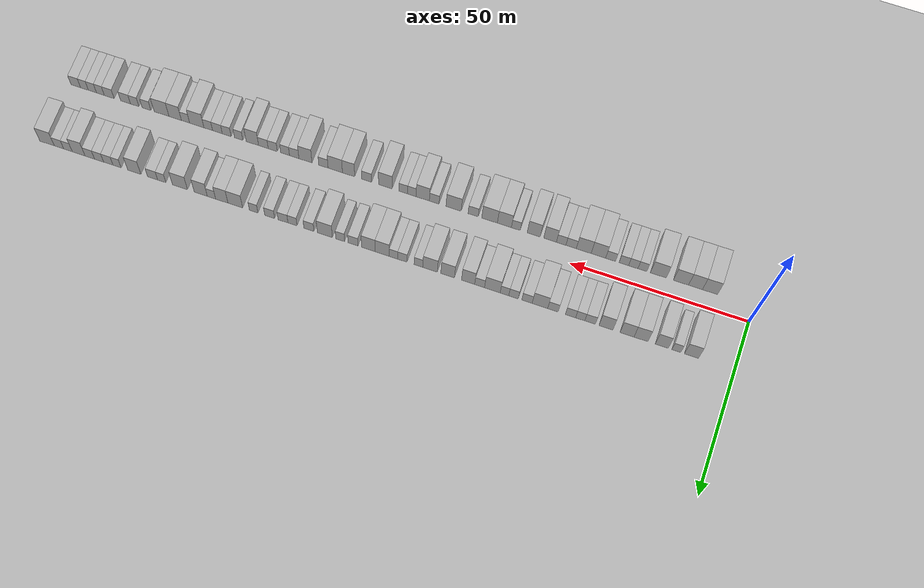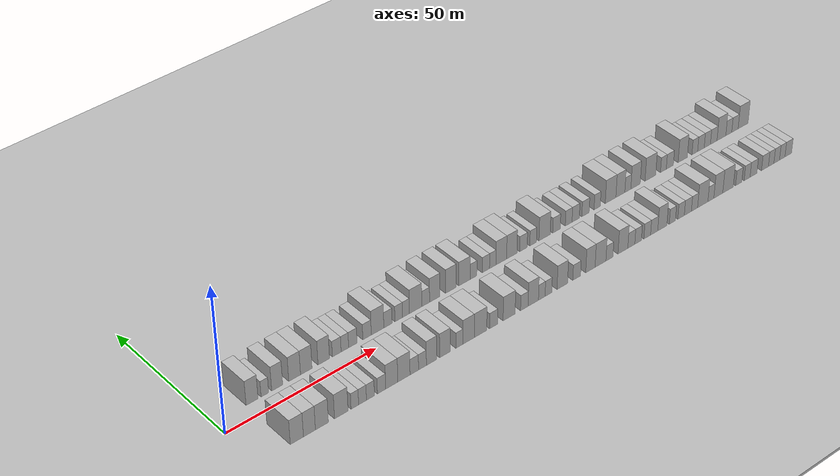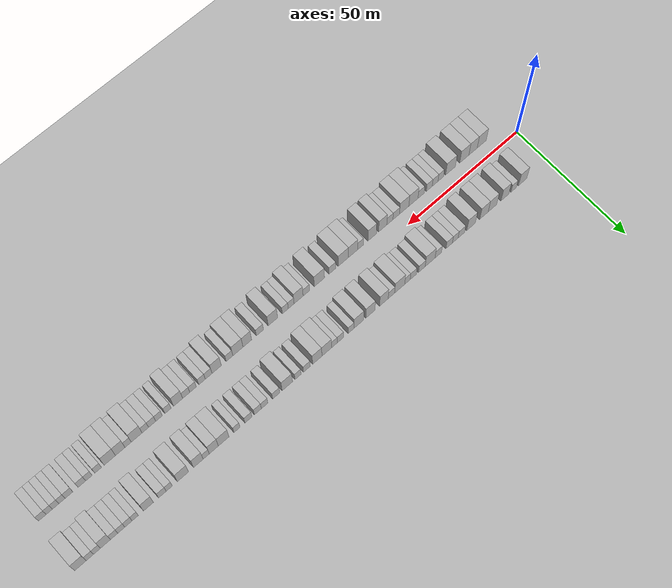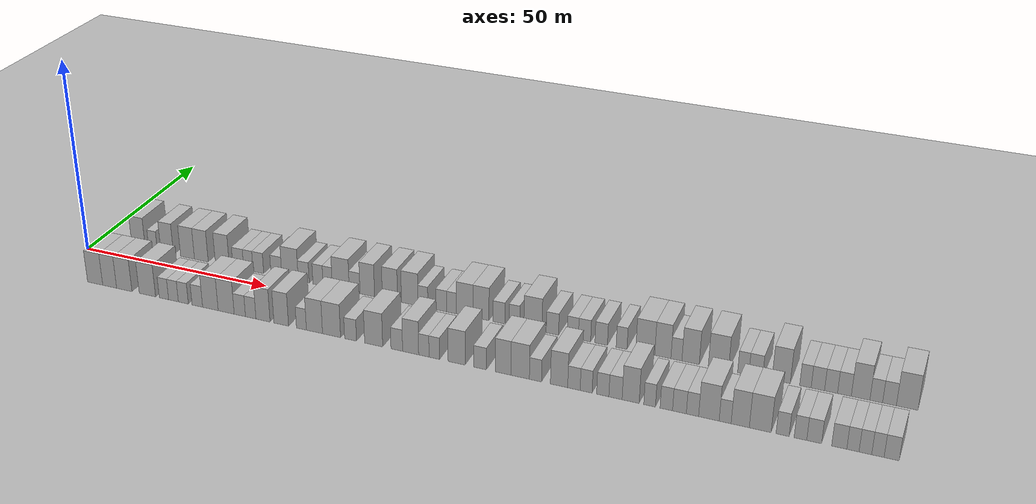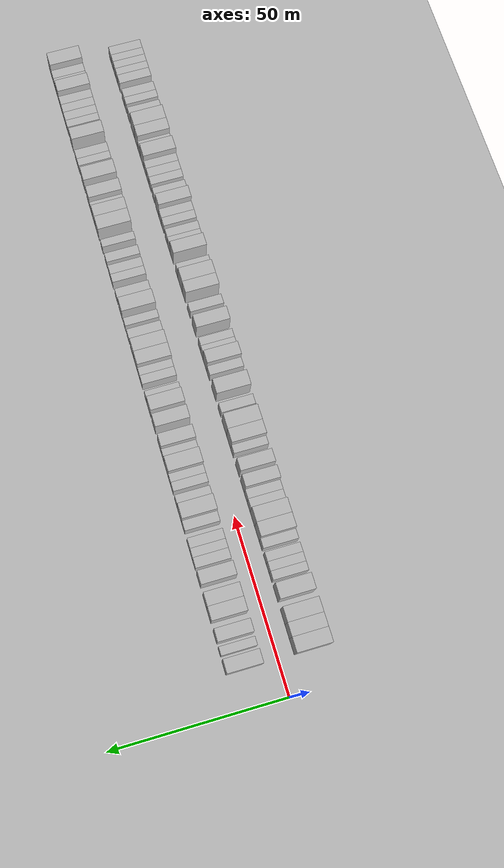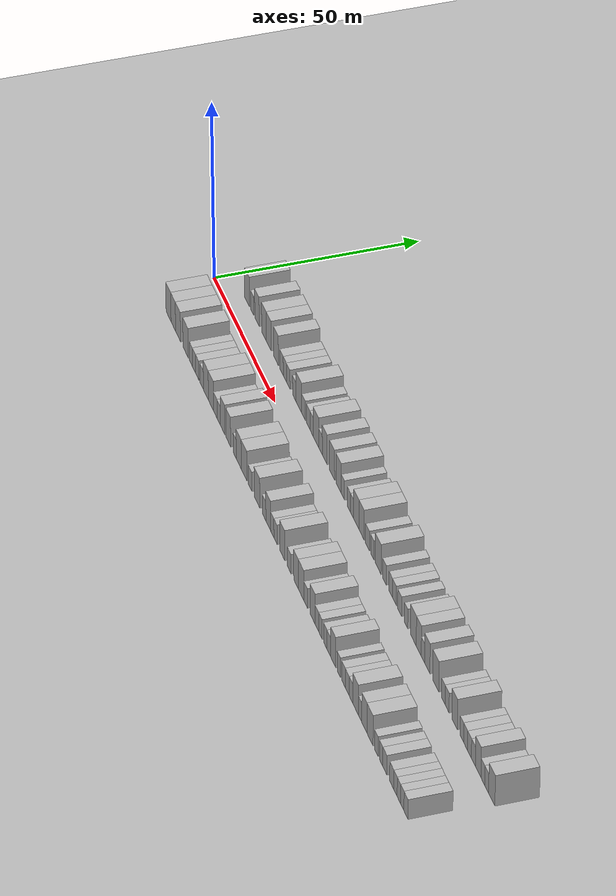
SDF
<?xml version="1.0" encoding="utf-8"?>

<sdf version="1.6">

   <world name="default">

      <gui fullscreen="0">

         <camera name="user_camera">

            <pose>-15 0 4.57585 0 0 0</pose>

            <view_controller>orbit</view_controller>

         </camera>

      </gui>

      <scene>

         <sky>

           <clouds>

             <speed>12</speed>

           </clouds>

         </sky>

         <ambient>0.4 0.4 0.4 1</ambient>

         <background>0.7 0.7 0.7 1</background>

         <shadows>1</shadows>

      </scene>

      <gravity>0 0 -9.8066</gravity>

      <magnetic_field>6e-06 2.3e-05 -4.2e-05</magnetic_field>

      <physics default="0" name="default_physics" type="ode">

         <ode>

            <solver>

               <type>quick</type>

               <iters>10</iters>

               <sor>1.0</sor>

               <use_dynamic_moi_rescaling>0</use_dynamic_moi_rescaling>

            </solver>

            <constraints>

               <cfm>0</cfm>

               <erp>0.2</erp>

               <contact_max_correcting_vel>100</contact_max_correcting_vel>

               <contact_surface_layer>0.001</contact_surface_layer>

            </constraints>

         </ode>

         <max_step_size>0.004</max_step_size>

         <real_time_factor>1</real_time_factor>

         <real_time_update_rate>250</real_time_update_rate>

      </physics>

      <light name="sun" type="directional">

         <cast_shadows>1</cast_shadows>

         <pose>0 0 10 0 0 0</pose>

         <diffuse>0.8 0.8 0.8 1</diffuse>

         <specular>0.2 0.2 0.2 1</specular>

         <attenuation>

            <range>1000</range>

            <constant>0.9</constant>

            <linear>0.01</linear>

            <quadratic>0.001</quadratic>

         </attenuation>

         <direction>-0.5 0.1 -0.9</direction>

      </light>

      <include>

         <name>ground_plane_1</name>

         <uri>model://HANNAS_ground_plane</uri>

         <pose>0 0 0  0 0 0</pose>

      </include>

      <include>

         <name>ground_plane_2</name>

         <uri>model://HANNAS_ground_plane</uri>

         <pose>100 0 0  0 0 0</pose>

      </include>

      <model name="building_1">

         <static>1</static>

         <pose frame="">11.9323 9.5000 0 0.000000 0.000000 1.570796</pose>

         <link name="link">

            <pose frame="">0 0 4.50 0 0 0</pose>

            <collision name="collision">

               <geometry>

                  <box>

                     <size>10.0000 3.8645 9.0000</size>

                  </box>

               </geometry>

               <max_contacts>10</max_contacts>

               <surface>

                  <contact>

                     <ode/>

                  </contact>

                  <bounce/>

                  <friction>

                     <torsional>

                        <ode/>

                     </torsional>

                     <ode/>

                  </friction>

               </surface>

            </collision>

            <visual name="visual">

               <cast_shadows>0</cast_shadows>

               <geometry>

                  <box>

                     <size>10.0000 3.8645 9.0000</size>

                  </box>

               </geometry>

               <material>

                  <script>

                     <uri>model://HANNAS_wall/materials/scripts</uri>

                     <uri>model://HANNAS_wall/materials/textures</uri>

                     <name>vrc/HANNAS_wall</name>

                  </script>

               </material>

            </visual>

            <self_collide>0</self_collide>

            <enable_wind>0</enable_wind>

            <kinematic>0</kinematic>

         </link>

      </model>

      <model name="building_2">

         <static>1</static>

         <pose frame="">16.0944 9.5000 0 0.000000 0.000000 1.570796</pose>

         <link name="link">

            <pose frame="">0 0 3.00 0 0 0</pose>

            <collision name="collision">

               <geometry>

                  <box>

                     <size>10.0000 2.4597 6.0000</size>

                  </box>

               </geometry>

               <max_contacts>10</max_contacts>

               <surface>

                  <contact>

                     <ode/>

                  </contact>

                  <bounce/>

                  <friction>

                     <torsional>

                        <ode/>

                     </torsional>

                     <ode/>

                  </friction>

               </surface>

            </collision>

            <visual name="visual">

               <cast_shadows>0</cast_shadows>

               <geometry>

                  <box>

                     <size>10.0000 2.4597 6.0000</size>

                  </box>

               </geometry>

               <material>

                  <script>

                     <uri>model://HANNAS_wall/materials/scripts</uri>

                     <uri>model://HANNAS_wall/materials/textures</uri>

                     <name>vrc/HANNAS_wall</name>

                  </script>

               </material>

            </visual>

            <self_collide>0</self_collide>

            <enable_wind>0</enable_wind>

            <kinematic>0</kinematic>

         </link>

      </model>

      <model name="building_3">

         <static>1</static>

         <pose frame="">20.1292 9.5000 0 0.000000 0.000000 1.570796</pose>

         <link name="link">

            <pose frame="">0 0 4.50 0 0 0</pose>

            <collision name="collision">

               <geometry>

                  <box>

                     <size>10.0000 3.6099 9.0000</size>

                  </box>

               </geometry>

               <max_contacts>10</max_contacts>

               <surface>

                  <contact>

                     <ode/>

                  </contact>

                  <bounce/>

                  <friction>

                     <torsional>

                        <ode/>

                     </torsional>

                     <ode/>

                  </friction>

               </surface>

            </collision>

            <visual name="visual">

               <cast_shadows>0</cast_shadows>

               <geometry>

                  <box>

                     <size>10.0000 3.6099 9.0000</size>

                  </box>

               </geometry>

               <material>

                  <script>

                     <uri>model://HANNAS_wall/materials/scripts</uri>

                     <uri>model://HANNAS_wall/materials/textures</uri>

                     <name>vrc/HANNAS_wall</name>

                  </script>

               </material>

            </visual>

            <self_collide>0</self_collide>

            <enable_wind>0</enable_wind>

            <kinematic>0</kinematic>

         </link>

      </model>

      <model name="building_4">

         <static>1</static>

         <pose frame="">25.8857 9.5000 0 0.000000 0.000000 1.570796</pose>

         <link name="link">

            <pose frame="">0 0 4.50 0 0 0</pose>

            <collision name="collision">

               <geometry>

                  <box>

                     <size>10.0000 3.9031 9.0000</size>

                  </box>

               </geometry>

               <max_contacts>10</max_contacts>

               <surface>

                  <contact>

                     <ode/>

                  </contact>

                  <bounce/>

                  <friction>

                     <torsional>

                        <ode/>

                     </torsional>

                     <ode/>

                  </friction>

               </surface>

            </collision>

            <visual name="visual">

               <cast_shadows>0</cast_shadows>

               <geometry>

                  <box>

                     <size>10.0000 3.9031 9.0000</size>

                  </box>

               </geometry>

               <material>

                  <script>

                     <uri>model://HANNAS_wall/materials/scripts</uri>

                     <uri>model://HANNAS_wall/materials/textures</uri>

                     <name>vrc/HANNAS_wall</name>

                  </script>

               </material>

            </visual>

            <self_collide>0</self_collide>

            <enable_wind>0</enable_wind>

            <kinematic>0</kinematic>

         </link>

      </model>

      <model name="building_5">

         <static>1</static>

         <pose frame="">29.7644 9.5000 0 0.000000 0.000000 1.570796</pose>

         <link name="link">

            <pose frame="">0 0 4.50 0 0 0</pose>

            <collision name="collision">

               <geometry>

                  <box>

                     <size>10.0000 3.8545 9.0000</size>

                  </box>

               </geometry>

               <max_contacts>10</max_contacts>

               <surface>

                  <contact>

                     <ode/>

                  </contact>

                  <bounce/>

                  <friction>

                     <torsional>

                        <ode/>

                     </torsional>

                     <ode/>

                  </friction>

               </surface>

            </collision>

            <visual name="visual">

               <cast_shadows>0</cast_shadows>

               <geometry>

                  <box>

                     <size>10.0000 3.8545 9.0000</size>

                  </box>

               </geometry>

               <material>

                  <script>

                     <uri>model://HANNAS_wall/materials/scripts</uri>

                     <uri>model://HANNAS_wall/materials/textures</uri>

                     <name>vrc/HANNAS_wall</name>

                  </script>

               </material>

            </visual>

            <self_collide>0</self_collide>

            <enable_wind>0</enable_wind>

            <kinematic>0</kinematic>

         </link>

      </model>

      <model name="building_6">

         <static>1</static>

         <pose frame="">35.6287 9.5000 0 0.000000 0.000000 1.570796</pose>

         <link name="link">

            <pose frame="">0 0 4.50 0 0 0</pose>

            <collision name="collision">

               <geometry>

                  <box>

                     <size>10.0000 3.8741 9.0000</size>

                  </box>

               </geometry>

               <max_contacts>10</max_contacts>

               <surface>

                  <contact>

                     <ode/>

                  </contact>

                  <bounce/>

                  <friction>

                     <torsional>

                        <ode/>

                     </torsional>

                     <ode/>

                  </friction>

               </surface>

            </collision>

            <visual name="visual">

               <cast_shadows>0</cast_shadows>

               <geometry>

                  <box>

                     <size>10.0000 3.8741 9.0000</size>

                  </box>

               </geometry>

               <material>

                  <script>

                     <uri>model://HANNAS_wall/materials/scripts</uri>

                     <uri>model://HANNAS_wall/materials/textures</uri>

                     <name>vrc/HANNAS_wall</name>

                  </script>

               </material>

            </visual>

            <self_collide>0</self_collide>

            <enable_wind>0</enable_wind>

            <kinematic>0</kinematic>

         </link>

      </model>

      <model name="building_7">

         <static>1</static>

         <pose frame="">40.0442 9.5000 0 0.000000 0.000000 1.570796</pose>

         <link name="link">

            <pose frame="">0 0 3.00 0 0 0</pose>

            <collision name="collision">

               <geometry>

                  <box>

                     <size>10.0000 2.9568 6.0000</size>

                  </box>

               </geometry>

               <max_contacts>10</max_contacts>

               <surface>

                  <contact>

                     <ode/>

                  </contact>

                  <bounce/>

                  <friction>

                     <torsional>

                        <ode/>

                     </torsional>

                     <ode/>

                  </friction>

               </surface>

            </collision>

            <visual name="visual">

               <cast_shadows>0</cast_shadows>

               <geometry>

                  <box>

                     <size>10.0000 2.9568 6.0000</size>

                  </box>

               </geometry>

               <material>

                  <script>

                     <uri>model://HANNAS_wall/materials/scripts</uri>

                     <uri>model://HANNAS_wall/materials/textures</uri>

                     <name>vrc/HANNAS_wall</name>

                  </script>

               </material>

            </visual>

            <self_collide>0</self_collide>

            <enable_wind>0</enable_wind>

            <kinematic>0</kinematic>

         </link>

      </model>

      <model name="building_8">

         <static>1</static>

         <pose frame="">42.8083 9.5000 0 0.000000 0.000000 1.570796</pose>

         <link name="link">

            <pose frame="">0 0 3.00 0 0 0</pose>

            <collision name="collision">

               <geometry>

                  <box>

                     <size>10.0000 2.5714 6.0000</size>

                  </box>

               </geometry>

               <max_contacts>10</max_contacts>

               <surface>

                  <contact>

                     <ode/>

                  </contact>

                  <bounce/>

                  <friction>

                     <torsional>

                        <ode/>

                     </torsional>

                     <ode/>

                  </friction>

               </surface>

            </collision>

            <visual name="visual">

               <cast_shadows>0</cast_shadows>

               <geometry>

                  <box>

                     <size>10.0000 2.5714 6.0000</size>

                  </box>

               </geometry>

               <material>

                  <script>

                     <uri>model://HANNAS_wall/materials/scripts</uri>

                     <uri>model://HANNAS_wall/materials/textures</uri>

                     <name>vrc/HANNAS_wall</name>

                  </script>

               </material>

            </visual>

            <self_collide>0</self_collide>

            <enable_wind>0</enable_wind>

            <kinematic>0</kinematic>

         </link>

      </model>

      <model name="building_9">

         <static>1</static>

         <pose frame="">45.5381 9.5000 0 0.000000 0.000000 1.570796</pose>

         <link name="link">

            <pose frame="">0 0 3.00 0 0 0</pose>

            <collision name="collision">

               <geometry>

                  <box>

                     <size>10.0000 2.8882 6.0000</size>

                  </box>

               </geometry>

               <max_contacts>10</max_contacts>

               <surface>

                  <contact>

                     <ode/>

                  </contact>

                  <bounce/>

                  <friction>

                     <torsional>

                        <ode/>

                     </torsional>

                     <ode/>

                  </friction>

               </surface>

            </collision>

            <visual name="visual">

               <cast_shadows>0</cast_shadows>

               <geometry>

                  <box>

                     <size>10.0000 2.8882 6.0000</size>

                  </box>

               </geometry>

               <material>

                  <script>

                     <uri>model://HANNAS_wall/materials/scripts</uri>

                     <uri>model://HANNAS_wall/materials/textures</uri>

                     <name>vrc/HANNAS_wall</name>

                  </script>

               </material>

            </visual>

            <self_collide>0</self_collide>

            <enable_wind>0</enable_wind>

            <kinematic>0</kinematic>

         </link>

      </model>

      <model name="building_10">

         <static>1</static>

         <pose frame="">50.4463 9.5000 0 0.000000 0.000000 1.570796</pose>

         <link name="link">

            <pose frame="">0 0 3.00 0 0 0</pose>

            <collision name="collision">

               <geometry>

                  <box>

                     <size>10.0000 2.9283 6.0000</size>

                  </box>

               </geometry>

               <max_contacts>10</max_contacts>

               <surface>

                  <contact>

                     <ode/>

                  </contact>

                  <bounce/>

                  <friction>

                     <torsional>

                        <ode/>

                     </torsional>

                     <ode/>

                  </friction>

               </surface>

            </collision>

            <visual name="visual">

               <cast_shadows>0</cast_shadows>

               <geometry>

                  <box>

                     <size>10.0000 2.9283 6.0000</size>

                  </box>

               </geometry>

               <material>

                  <script>

                     <uri>model://HANNAS_wall/materials/scripts</uri>

                     <uri>model://HANNAS_wall/materials/textures</uri>

                     <name>vrc/HANNAS_wall</name>

                  </script>

               </material>

            </visual>

            <self_collide>0</self_collide>

            <enable_wind>0</enable_wind>

            <kinematic>0</kinematic>

         </link>

      </model>

      <model name="building_11">

         <static>1</static>

         <pose frame="">54.1067 9.5000 0 0.000000 0.000000 1.570796</pose>

         <link name="link">

            <pose frame="">0 0 4.50 0 0 0</pose>

            <collision name="collision">

               <geometry>

                  <box>

                     <size>10.0000 4.3924 9.0000</size>

                  </box>

               </geometry>

               <max_contacts>10</max_contacts>

               <surface>

                  <contact>

                     <ode/>

                  </contact>

                  <bounce/>

                  <friction>

                     <torsional>

                        <ode/>

                     </torsional>

                     <ode/>

                  </friction>

               </surface>

            </collision>

            <visual name="visual">

               <cast_shadows>0</cast_shadows>

               <geometry>

                  <box>

                     <size>10.0000 4.3924 9.0000</size>

                  </box>

               </geometry>

               <material>

                  <script>

                     <uri>model://HANNAS_wall/materials/scripts</uri>

                     <uri>model://HANNAS_wall/materials/textures</uri>

                     <name>vrc/HANNAS_wall</name>

                  </script>

               </material>

            </visual>

            <self_collide>0</self_collide>

            <enable_wind>0</enable_wind>

            <kinematic>0</kinematic>

         </link>

      </model>

      <model name="building_12">

         <static>1</static>

         <pose frame="">57.7570 9.5000 0 0.000000 0.000000 1.570796</pose>

         <link name="link">

            <pose frame="">0 0 3.00 0 0 0</pose>

            <collision name="collision">

               <geometry>

                  <box>

                     <size>10.0000 2.9081 6.0000</size>

                  </box>

               </geometry>

               <max_contacts>10</max_contacts>

               <surface>

                  <contact>

                     <ode/>

                  </contact>

                  <bounce/>

                  <friction>

                     <torsional>

                        <ode/>

                     </torsional>

                     <ode/>

                  </friction>

               </surface>

            </collision>

            <visual name="visual">

               <cast_shadows>0</cast_shadows>

               <geometry>

                  <box>

                     <size>10.0000 2.9081 6.0000</size>

                  </box>

               </geometry>

               <material>

                  <script>

                     <uri>model://HANNAS_wall/materials/scripts</uri>

                     <uri>model://HANNAS_wall/materials/textures</uri>

                     <name>vrc/HANNAS_wall</name>

                  </script>

               </material>

            </visual>

            <self_collide>0</self_collide>

            <enable_wind>0</enable_wind>

            <kinematic>0</kinematic>

         </link>

      </model>

      <model name="building_13">

         <static>1</static>

         <pose frame="">61.5493 9.5000 0 0.000000 0.000000 1.570796</pose>

         <link name="link">

            <pose frame="">0 0 3.00 0 0 0</pose>

            <collision name="collision">

               <geometry>

                  <box>

                     <size>10.0000 2.6766 6.0000</size>

                  </box>

               </geometry>

               <max_contacts>10</max_contacts>

               <surface>

                  <contact>

                     <ode/>

                  </contact>

                  <bounce/>

                  <friction>

                     <torsional>

                        <ode/>

                     </torsional>

                     <ode/>

                  </friction>

               </surface>

            </collision>

            <visual name="visual">

               <cast_shadows>0</cast_shadows>

               <geometry>

                  <box>

                     <size>10.0000 2.6766 6.0000</size>

                  </box>

               </geometry>

               <material>

                  <script>

                     <uri>model://HANNAS_wall/materials/scripts</uri>

                     <uri>model://HANNAS_wall/materials/textures</uri>

                     <name>vrc/HANNAS_wall</name>

                  </script>

               </material>

            </visual>

            <self_collide>0</self_collide>

            <enable_wind>0</enable_wind>

            <kinematic>0</kinematic>

         </link>

      </model>

      <model name="building_14">

         <static>1</static>

         <pose frame="">64.1087 9.5000 0 0.000000 0.000000 1.570796</pose>

         <link name="link">

            <pose frame="">0 0 3.00 0 0 0</pose>

            <collision name="collision">

               <geometry>

                  <box>

                     <size>10.0000 2.4421 6.0000</size>

                  </box>

               </geometry>

               <max_contacts>10</max_contacts>

               <surface>

                  <contact>

                     <ode/>

                  </contact>

                  <bounce/>

                  <friction>

                     <torsional>

                        <ode/>

                     </torsional>

                     <ode/>

                  </friction>

               </surface>

            </collision>

            <visual name="visual">

               <cast_shadows>0</cast_shadows>

               <geometry>

                  <box>

                     <size>10.0000 2.4421 6.0000</size>

                  </box>

               </geometry>

               <material>

                  <script>

                     <uri>model://HANNAS_wall/materials/scripts</uri>

                     <uri>model://HANNAS_wall/materials/textures</uri>

                     <name>vrc/HANNAS_wall</name>

                  </script>

               </material>

            </visual>

            <self_collide>0</self_collide>

            <enable_wind>0</enable_wind>

            <kinematic>0</kinematic>

         </link>

      </model>

      <model name="building_15">

         <static>1</static>

         <pose frame="">67.5504 9.5000 0 0.000000 0.000000 1.570796</pose>

         <link name="link">

            <pose frame="">0 0 4.50 0 0 0</pose>

            <collision name="collision">

               <geometry>

                  <box>

                     <size>10.0000 4.4414 9.0000</size>

                  </box>

               </geometry>

               <max_contacts>10</max_contacts>

               <surface>

                  <contact>

                     <ode/>

                  </contact>

                  <bounce/>

                  <friction>

                     <torsional>

                        <ode/>

                     </torsional>

                     <ode/>

                  </friction>

               </surface>

            </collision>

            <visual name="visual">

               <cast_shadows>0</cast_shadows>

               <geometry>

                  <box>

                     <size>10.0000 4.4414 9.0000</size>

                  </box>

               </geometry>

               <material>

                  <script>

                     <uri>model://HANNAS_wall/materials/scripts</uri>

                     <uri>model://HANNAS_wall/materials/textures</uri>

                     <name>vrc/HANNAS_wall</name>

                  </script>

               </material>

            </visual>

            <self_collide>0</self_collide>

            <enable_wind>0</enable_wind>

            <kinematic>0</kinematic>

         </link>

      </model>

      <model name="building_16">

         <static>1</static>

         <pose frame="">71.1654 9.5000 0 0.000000 0.000000 1.570796</pose>

         <link name="link">

            <pose frame="">0 0 3.00 0 0 0</pose>

            <collision name="collision">

               <geometry>

                  <box>

                     <size>10.0000 2.7886 6.0000</size>

                  </box>

               </geometry>

               <max_contacts>10</max_contacts>

               <surface>

                  <contact>

                     <ode/>

                  </contact>

                  <bounce/>

                  <friction>

                     <torsional>

                        <ode/>

                     </torsional>

                     <ode/>

                  </friction>

               </surface>

            </collision>

            <visual name="visual">

               <cast_shadows>0</cast_shadows>

               <geometry>

                  <box>

                     <size>10.0000 2.7886 6.0000</size>

                  </box>

               </geometry>

               <material>

                  <script>

                     <uri>model://HANNAS_wall/materials/scripts</uri>

                     <uri>model://HANNAS_wall/materials/textures</uri>

                     <name>vrc/HANNAS_wall</name>

                  </script>

               </material>

            </visual>

            <self_collide>0</self_collide>

            <enable_wind>0</enable_wind>

            <kinematic>0</kinematic>

         </link>

      </model>

      <model name="building_17">

         <static>1</static>

         <pose frame="">74.4422 9.5000 0 0.000000 0.000000 1.570796</pose>

         <link name="link">

            <pose frame="">0 0 4.50 0 0 0</pose>

            <collision name="collision">

               <geometry>

                  <box>

                     <size>10.0000 3.7651 9.0000</size>

                  </box>

               </geometry>

               <max_contacts>10</max_contacts>

               <surface>

                  <contact>

                     <ode/>

                  </contact>

                  <bounce/>

                  <friction>

                     <torsional>

                        <ode/>

                     </torsional>

                     <ode/>

                  </friction>

               </surface>

            </collision>

            <visual name="visual">

               <cast_shadows>0</cast_shadows>

               <geometry>

                  <box>

                     <size>10.0000 3.7651 9.0000</size>

                  </box>

               </geometry>

               <material>

                  <script>

                     <uri>model://HANNAS_wall/materials/scripts</uri>

                     <uri>model://HANNAS_wall/materials/textures</uri>

                     <name>vrc/HANNAS_wall</name>

                  </script>

               </material>

            </visual>

            <self_collide>0</self_collide>

            <enable_wind>0</enable_wind>

            <kinematic>0</kinematic>

         </link>

      </model>

      <model name="building_18">

         <static>1</static>

         <pose frame="">80.2710 9.5000 0 0.000000 0.000000 1.570796</pose>

         <link name="link">

            <pose frame="">0 0 4.50 0 0 0</pose>

            <collision name="collision">

               <geometry>

                  <box>

                     <size>10.0000 3.8924 9.0000</size>

                  </box>

               </geometry>

               <max_contacts>10</max_contacts>

               <surface>

                  <contact>

                     <ode/>

                  </contact>

                  <bounce/>

                  <friction>

                     <torsional>

                        <ode/>

                     </torsional>

                     <ode/>

                  </friction>

               </surface>

            </collision>

            <visual name="visual">

               <cast_shadows>0</cast_shadows>

               <geometry>

                  <box>

                     <size>10.0000 3.8924 9.0000</size>

                  </box>

               </geometry>

               <material>

                  <script>

                     <uri>model://HANNAS_wall/materials/scripts</uri>

                     <uri>model://HANNAS_wall/materials/textures</uri>

                     <name>vrc/HANNAS_wall</name>

                  </script>

               </material>

            </visual>

            <self_collide>0</self_collide>

            <enable_wind>0</enable_wind>

            <kinematic>0</kinematic>

         </link>

      </model>

      <model name="building_19">

         <static>1</static>

         <pose frame="">85.3004 9.5000 0 0.000000 0.000000 1.570796</pose>

         <link name="link">

            <pose frame="">0 0 4.50 0 0 0</pose>

            <collision name="collision">

               <geometry>

                  <box>

                     <size>10.0000 4.1664 9.0000</size>

                  </box>

               </geometry>

               <max_contacts>10</max_contacts>

               <surface>

                  <contact>

                     <ode/>

                  </contact>

                  <bounce/>

                  <friction>

                     <torsional>

                        <ode/>

                     </torsional>

                     <ode/>

                  </friction>

               </surface>

            </collision>

            <visual name="visual">

               <cast_shadows>0</cast_shadows>

               <geometry>

                  <box>

                     <size>10.0000 4.1664 9.0000</size>

                  </box>

               </geometry>

               <material>

                  <script>

                     <uri>model://HANNAS_wall/materials/scripts</uri>

                     <uri>model://HANNAS_wall/materials/textures</uri>

                     <name>vrc/HANNAS_wall</name>

                  </script>

               </material>

            </visual>

            <self_collide>0</self_collide>

            <enable_wind>0</enable_wind>

            <kinematic>0</kinematic>

         </link>

      </model>

      <model name="building_20">

         <static>1</static>

         <pose frame="">88.6267 9.5000 0 0.000000 0.000000 1.570796</pose>

         <link name="link">

            <pose frame="">0 0 3.00 0 0 0</pose>

            <collision name="collision">

               <geometry>

                  <box>

                     <size>10.0000 2.4862 6.0000</size>

                  </box>

               </geometry>

               <max_contacts>10</max_contacts>

               <surface>

                  <contact>

                     <ode/>

                  </contact>

                  <bounce/>

                  <friction>

                     <torsional>

                        <ode/>

                     </torsional>

                     <ode/>

                  </friction>

               </surface>

            </collision>

            <visual name="visual">

               <cast_shadows>0</cast_shadows>

               <geometry>

                  <box>

                     <size>10.0000 2.4862 6.0000</size>

                  </box>

               </geometry>

               <material>

                  <script>

                     <uri>model://HANNAS_wall/materials/scripts</uri>

                     <uri>model://HANNAS_wall/materials/textures</uri>

                     <name>vrc/HANNAS_wall</name>

                  </script>

               </material>

            </visual>

            <self_collide>0</self_collide>

            <enable_wind>0</enable_wind>

            <kinematic>0</kinematic>

         </link>

      </model>

      <model name="building_21">

         <static>1</static>

         <pose frame="">93.2299 9.5000 0 0.000000 0.000000 1.570796</pose>

         <link name="link">

            <pose frame="">0 0 3.00 0 0 0</pose>

            <collision name="collision">

               <geometry>

                  <box>

                     <size>10.0000 2.7202 6.0000</size>

                  </box>

               </geometry>

               <max_contacts>10</max_contacts>

               <surface>

                  <contact>

                     <ode/>

                  </contact>

                  <bounce/>

                  <friction>

                     <torsional>

                        <ode/>

                     </torsional>

                     <ode/>

                  </friction>

               </surface>

            </collision>

            <visual name="visual">

               <cast_shadows>0</cast_shadows>

               <geometry>

                  <box>

                     <size>10.0000 2.7202 6.0000</size>

                  </box>

               </geometry>

               <material>

                  <script>

                     <uri>model://HANNAS_wall/materials/scripts</uri>

                     <uri>model://HANNAS_wall/materials/textures</uri>

                     <name>vrc/HANNAS_wall</name>

                  </script>

               </material>

            </visual>

            <self_collide>0</self_collide>

            <enable_wind>0</enable_wind>

            <kinematic>0</kinematic>

         </link>

      </model>

      <model name="building_22">

         <static>1</static>

         <pose frame="">95.7969 9.5000 0 0.000000 0.000000 1.570796</pose>

         <link name="link">

            <pose frame="">0 0 3.00 0 0 0</pose>

            <collision name="collision">

               <geometry>

                  <box>

                     <size>10.0000 2.4138 6.0000</size>

                  </box>

               </geometry>

               <max_contacts>10</max_contacts>

               <surface>

                  <contact>

                     <ode/>

                  </contact>

                  <bounce/>

                  <friction>

                     <torsional>

                        <ode/>

                     </torsional>

                     <ode/>

                  </friction>

               </surface>

            </collision>

            <visual name="visual">

               <cast_shadows>0</cast_shadows>

               <geometry>

                  <box>

                     <size>10.0000 2.4138 6.0000</size>

                  </box>

               </geometry>

               <material>

                  <script>

                     <uri>model://HANNAS_wall/materials/scripts</uri>

                     <uri>model://HANNAS_wall/materials/textures</uri>

                     <name>vrc/HANNAS_wall</name>

                  </script>

               </material>

            </visual>

            <self_collide>0</self_collide>

            <enable_wind>0</enable_wind>

            <kinematic>0</kinematic>

         </link>

      </model>

      <model name="building_23">

         <static>1</static>

         <pose frame="">99.0238 9.5000 0 0.000000 0.000000 1.570796</pose>

         <link name="link">

            <pose frame="">0 0 4.50 0 0 0</pose>

            <collision name="collision">

               <geometry>

                  <box>

                     <size>10.0000 4.0401 9.0000</size>

                  </box>

               </geometry>

               <max_contacts>10</max_contacts>

               <surface>

                  <contact>

                     <ode/>

                  </contact>

                  <bounce/>

                  <friction>

                     <torsional>

                        <ode/>

                     </torsional>

                     <ode/>

                  </friction>

               </surface>

            </collision>

            <visual name="visual">

               <cast_shadows>0</cast_shadows>

               <geometry>

                  <box>

                     <size>10.0000 4.0401 9.0000</size>

                  </box>

               </geometry>

               <material>

                  <script>

                     <uri>model://HANNAS_wall/materials/scripts</uri>

                     <uri>model://HANNAS_wall/materials/textures</uri>

                     <name>vrc/HANNAS_wall</name>

                  </script>

               </material>

            </visual>

            <self_collide>0</self_collide>

            <enable_wind>0</enable_wind>

            <kinematic>0</kinematic>

         </link>

      </model>

      <model name="building_24">

         <static>1</static>

         <pose frame="">103.0161 9.5000 0 0.000000 0.000000 1.570796</pose>

         <link name="link">

            <pose frame="">0 0 4.50 0 0 0</pose>

            <collision name="collision">

               <geometry>

                  <box>

                     <size>10.0000 3.9446 9.0000</size>

                  </box>

               </geometry>

               <max_contacts>10</max_contacts>

               <surface>

                  <contact>

                     <ode/>

                  </contact>

                  <bounce/>

                  <friction>

                     <torsional>

                        <ode/>

                     </torsional>

                     <ode/>

                  </friction>

               </surface>

            </collision>

            <visual name="visual">

               <cast_shadows>0</cast_shadows>

               <geometry>

                  <box>

                     <size>10.0000 3.9446 9.0000</size>

                  </box>

               </geometry>

               <material>

                  <script>

                     <uri>model://HANNAS_wall/materials/scripts</uri>

                     <uri>model://HANNAS_wall/materials/textures</uri>

                     <name>vrc/HANNAS_wall</name>

                  </script>

               </material>

            </visual>

            <self_collide>0</self_collide>

            <enable_wind>0</enable_wind>

            <kinematic>0</kinematic>

         </link>

      </model>

      <model name="building_25">

         <static>1</static>

         <pose frame="">107.4383 9.5000 0 0.000000 0.000000 1.570796</pose>

         <link name="link">

            <pose frame="">0 0 3.00 0 0 0</pose>

            <collision name="collision">

               <geometry>

                  <box>

                     <size>10.0000 2.8997 6.0000</size>

                  </box>

               </geometry>

               <max_contacts>10</max_contacts>

               <surface>

                  <contact>

                     <ode/>

                  </contact>

                  <bounce/>

                  <friction>

                     <torsional>

                        <ode/>

                     </torsional>

                     <ode/>

                  </friction>

               </surface>

            </collision>

            <visual name="visual">

               <cast_shadows>0</cast_shadows>

               <geometry>

                  <box>

                     <size>10.0000 2.8997 6.0000</size>

                  </box>

               </geometry>

               <material>

                  <script>

                     <uri>model://HANNAS_wall/materials/scripts</uri>

                     <uri>model://HANNAS_wall/materials/textures</uri>

                     <name>vrc/HANNAS_wall</name>

                  </script>

               </material>

            </visual>

            <self_collide>0</self_collide>

            <enable_wind>0</enable_wind>

            <kinematic>0</kinematic>

         </link>

      </model>

      <model name="building_26">

         <static>1</static>

         <pose frame="">111.1577 9.5000 0 0.000000 0.000000 1.570796</pose>

         <link name="link">

            <pose frame="">0 0 3.00 0 0 0</pose>

            <collision name="collision">

               <geometry>

                  <box>

                     <size>10.0000 2.5390 6.0000</size>

                  </box>

               </geometry>

               <max_contacts>10</max_contacts>

               <surface>

                  <contact>

                     <ode/>

                  </contact>

                  <bounce/>

                  <friction>

                     <torsional>

                        <ode/>

                     </torsional>

                     <ode/>

                  </friction>

               </surface>

            </collision>

            <visual name="visual">

               <cast_shadows>0</cast_shadows>

               <geometry>

                  <box>

                     <size>10.0000 2.5390 6.0000</size>

                  </box>

               </geometry>

               <material>

                  <script>

                     <uri>model://HANNAS_wall/materials/scripts</uri>

                     <uri>model://HANNAS_wall/materials/textures</uri>

                     <name>vrc/HANNAS_wall</name>

                  </script>

               </material>

            </visual>

            <self_collide>0</self_collide>

            <enable_wind>0</enable_wind>

            <kinematic>0</kinematic>

         </link>

      </model>

      <model name="building_27">

         <static>1</static>

         <pose frame="">115.5979 9.5000 0 0.000000 0.000000 1.570796</pose>

         <link name="link">

            <pose frame="">0 0 4.50 0 0 0</pose>

            <collision name="collision">

               <geometry>

                  <box>

                     <size>10.0000 4.3414 9.0000</size>

                  </box>

               </geometry>

               <max_contacts>10</max_contacts>

               <surface>

                  <contact>

                     <ode/>

                  </contact>

                  <bounce/>

                  <friction>

                     <torsional>

                        <ode/>

                     </torsional>

                     <ode/>

                  </friction>

               </surface>

            </collision>

            <visual name="visual">

               <cast_shadows>0</cast_shadows>

               <geometry>

                  <box>

                     <size>10.0000 4.3414 9.0000</size>

                  </box>

               </geometry>

               <material>

                  <script>

                     <uri>model://HANNAS_wall/materials/scripts</uri>

                     <uri>model://HANNAS_wall/materials/textures</uri>

                     <name>vrc/HANNAS_wall</name>

                  </script>

               </material>

            </visual>

            <self_collide>0</self_collide>

            <enable_wind>0</enable_wind>

            <kinematic>0</kinematic>

         </link>

      </model>

      <model name="building_28">

         <static>1</static>

         <pose frame="">120.2355 9.5000 0 0.000000 0.000000 1.570796</pose>

         <link name="link">

            <pose frame="">0 0 3.00 0 0 0</pose>

            <collision name="collision">

               <geometry>

                  <box>

                     <size>10.0000 2.9337 6.0000</size>

                  </box>

               </geometry>

               <max_contacts>10</max_contacts>

               <surface>

                  <contact>

                     <ode/>

                  </contact>

                  <bounce/>

                  <friction>

                     <torsional>

                        <ode/>

                     </torsional>

                     <ode/>

                  </friction>

               </surface>

            </collision>

            <visual name="visual">

               <cast_shadows>0</cast_shadows>

               <geometry>

                  <box>

                     <size>10.0000 2.9337 6.0000</size>

                  </box>

               </geometry>

               <material>

                  <script>

                     <uri>model://HANNAS_wall/materials/scripts</uri>

                     <uri>model://HANNAS_wall/materials/textures</uri>

                     <name>vrc/HANNAS_wall</name>

                  </script>

               </material>

            </visual>

            <self_collide>0</self_collide>

            <enable_wind>0</enable_wind>

            <kinematic>0</kinematic>

         </link>

      </model>

      <model name="building_29">

         <static>1</static>

         <pose frame="">125.0300 9.5000 0 0.000000 0.000000 1.570796</pose>

         <link name="link">

            <pose frame="">0 0 3.00 0 0 0</pose>

            <collision name="collision">

               <geometry>

                  <box>

                     <size>10.0000 2.6554 6.0000</size>

                  </box>

               </geometry>

               <max_contacts>10</max_contacts>

               <surface>

                  <contact>

                     <ode/>

                  </contact>

                  <bounce/>

                  <friction>

                     <torsional>

                        <ode/>

                     </torsional>

                     <ode/>

                  </friction>

               </surface>

            </collision>

            <visual name="visual">

               <cast_shadows>0</cast_shadows>

               <geometry>

                  <box>

                     <size>10.0000 2.6554 6.0000</size>

                  </box>

               </geometry>

               <material>

                  <script>

                     <uri>model://HANNAS_wall/materials/scripts</uri>

                     <uri>model://HANNAS_wall/materials/textures</uri>

                     <name>vrc/HANNAS_wall</name>

                  </script>

               </material>

            </visual>

            <self_collide>0</self_collide>

            <enable_wind>0</enable_wind>

            <kinematic>0</kinematic>

         </link>

      </model>

      <model name="building_30">

         <static>1</static>

         <pose frame="">127.7950 9.5000 0 0.000000 0.000000 1.570796</pose>

         <link name="link">

            <pose frame="">0 0 3.00 0 0 0</pose>

            <collision name="collision">

               <geometry>

                  <box>

                     <size>10.0000 2.8746 6.0000</size>

                  </box>

               </geometry>

               <max_contacts>10</max_contacts>

               <surface>

                  <contact>

                     <ode/>

                  </contact>

                  <bounce/>

                  <friction>

                     <torsional>

                        <ode/>

                     </torsional>

                     <ode/>

                  </friction>

               </surface>

            </collision>

            <visual name="visual">

               <cast_shadows>0</cast_shadows>

               <geometry>

                  <box>

                     <size>10.0000 2.8746 6.0000</size>

                  </box>

               </geometry>

               <material>

                  <script>

                     <uri>model://HANNAS_wall/materials/scripts</uri>

                     <uri>model://HANNAS_wall/materials/textures</uri>

                     <name>vrc/HANNAS_wall</name>

                  </script>

               </material>

            </visual>

            <self_collide>0</self_collide>

            <enable_wind>0</enable_wind>

            <kinematic>0</kinematic>

         </link>

      </model>

      <model name="building_31">

         <static>1</static>

         <pose frame="">131.6793 9.5000 0 0.000000 0.000000 1.570796</pose>

         <link name="link">

            <pose frame="">0 0 3.00 0 0 0</pose>

            <collision name="collision">

               <geometry>

                  <box>

                     <size>10.0000 2.8940 6.0000</size>

                  </box>

               </geometry>

               <max_contacts>10</max_contacts>

               <surface>

                  <contact>

                     <ode/>

                  </contact>

                  <bounce/>

                  <friction>

                     <torsional>

                        <ode/>

                     </torsional>

                     <ode/>

                  </friction>

               </surface>

            </collision>

            <visual name="visual">

               <cast_shadows>0</cast_shadows>

               <geometry>

                  <box>

                     <size>10.0000 2.8940 6.0000</size>

                  </box>

               </geometry>

               <material>

                  <script>

                     <uri>model://HANNAS_wall/materials/scripts</uri>

                     <uri>model://HANNAS_wall/materials/textures</uri>

                     <name>vrc/HANNAS_wall</name>

                  </script>

               </material>

            </visual>

            <self_collide>0</self_collide>

            <enable_wind>0</enable_wind>

            <kinematic>0</kinematic>

         </link>

      </model>

      <model name="building_32">

         <static>1</static>

         <pose frame="">136.3744 9.5000 0 0.000000 0.000000 1.570796</pose>

         <link name="link">

            <pose frame="">0 0 3.00 0 0 0</pose>

            <collision name="collision">

               <geometry>

                  <box>

                     <size>10.0000 2.4963 6.0000</size>

                  </box>

               </geometry>

               <max_contacts>10</max_contacts>

               <surface>

                  <contact>

                     <ode/>

                  </contact>

                  <bounce/>

                  <friction>

                     <torsional>

                        <ode/>

                     </torsional>

                     <ode/>

                  </friction>

               </surface>

            </collision>

            <visual name="visual">

               <cast_shadows>0</cast_shadows>

               <geometry>

                  <box>

                     <size>10.0000 2.4963 6.0000</size>

                  </box>

               </geometry>

               <material>

                  <script>

                     <uri>model://HANNAS_wall/materials/scripts</uri>

                     <uri>model://HANNAS_wall/materials/textures</uri>

                     <name>vrc/HANNAS_wall</name>

                  </script>

               </material>

            </visual>

            <self_collide>0</self_collide>

            <enable_wind>0</enable_wind>

            <kinematic>0</kinematic>

         </link>

      </model>

      <model name="building_33">

         <static>1</static>

         <pose frame="">141.7789 9.5000 0 0.000000 0.000000 1.570796</pose>

         <link name="link">

            <pose frame="">0 0 4.50 0 0 0</pose>

            <collision name="collision">

               <geometry>

                  <box>

                     <size>10.0000 4.3128 9.0000</size>

                  </box>

               </geometry>

               <max_contacts>10</max_contacts>

               <surface>

                  <contact>

                     <ode/>

                  </contact>

                  <bounce/>

                  <friction>

                     <torsional>

                        <ode/>

                     </torsional>

                     <ode/>

                  </friction>

               </surface>

            </collision>

            <visual name="visual">

               <cast_shadows>0</cast_shadows>

               <geometry>

                  <box>

                     <size>10.0000 4.3128 9.0000</size>

                  </box>

               </geometry>

               <material>

                  <script>

                     <uri>model://HANNAS_wall/materials/scripts</uri>

                     <uri>model://HANNAS_wall/materials/textures</uri>

                     <name>vrc/HANNAS_wall</name>

                  </script>

               </material>

            </visual>

            <self_collide>0</self_collide>

            <enable_wind>0</enable_wind>

            <kinematic>0</kinematic>

         </link>

      </model>

      <model name="building_34">

         <static>1</static>

         <pose frame="">145.7628 9.5000 0 0.000000 0.000000 1.570796</pose>

         <link name="link">

            <pose frame="">0 0 4.50 0 0 0</pose>

            <collision name="collision">

               <geometry>

                  <box>

                     <size>10.0000 3.6548 9.0000</size>

                  </box>

               </geometry>

               <max_contacts>10</max_contacts>

               <surface>

                  <contact>

                     <ode/>

                  </contact>

                  <bounce/>

                  <friction>

                     <torsional>

                        <ode/>

                     </torsional>

                     <ode/>

                  </friction>

               </surface>

            </collision>

            <visual name="visual">

               <cast_shadows>0</cast_shadows>

               <geometry>

                  <box>

                     <size>10.0000 3.6548 9.0000</size>

                  </box>

               </geometry>

               <material>

                  <script>

                     <uri>model://HANNAS_wall/materials/scripts</uri>

                     <uri>model://HANNAS_wall/materials/textures</uri>

                     <name>vrc/HANNAS_wall</name>

                  </script>

               </material>

            </visual>

            <self_collide>0</self_collide>

            <enable_wind>0</enable_wind>

            <kinematic>0</kinematic>

         </link>

      </model>

      <model name="building_35">

         <static>1</static>

         <pose frame="">148.8193 9.5000 0 0.000000 0.000000 1.570796</pose>

         <link name="link">

            <pose frame="">0 0 3.00 0 0 0</pose>

            <collision name="collision">

               <geometry>

                  <box>

                     <size>10.0000 2.4582 6.0000</size>

                  </box>

               </geometry>

               <max_contacts>10</max_contacts>

               <surface>

                  <contact>

                     <ode/>

                  </contact>

                  <bounce/>

                  <friction>

                     <torsional>

                        <ode/>

                     </torsional>

                     <ode/>

                  </friction>

               </surface>

            </collision>

            <visual name="visual">

               <cast_shadows>0</cast_shadows>

               <geometry>

                  <box>

                     <size>10.0000 2.4582 6.0000</size>

                  </box>

               </geometry>

               <material>

                  <script>

                     <uri>model://HANNAS_wall/materials/scripts</uri>

                     <uri>model://HANNAS_wall/materials/textures</uri>

                     <name>vrc/HANNAS_wall</name>

                  </script>

               </material>

            </visual>

            <self_collide>0</self_collide>

            <enable_wind>0</enable_wind>

            <kinematic>0</kinematic>

         </link>

      </model>

      <model name="building_36">

         <static>1</static>

         <pose frame="">151.9762 9.5000 0 0.000000 0.000000 1.570796</pose>

         <link name="link">

            <pose frame="">0 0 4.50 0 0 0</pose>

            <collision name="collision">

               <geometry>

                  <box>

                     <size>10.0000 3.8558 9.0000</size>

                  </box>

               </geometry>

               <max_contacts>10</max_contacts>

               <surface>

                  <contact>

                     <ode/>

                  </contact>

                  <bounce/>

                  <friction>

                     <torsional>

                        <ode/>

                     </torsional>

                     <ode/>

                  </friction>

               </surface>

            </collision>

            <visual name="visual">

               <cast_shadows>0</cast_shadows>

               <geometry>

                  <box>

                     <size>10.0000 3.8558 9.0000</size>

                  </box>

               </geometry>

               <material>

                  <script>

                     <uri>model://HANNAS_wall/materials/scripts</uri>

                     <uri>model://HANNAS_wall/materials/textures</uri>

                     <name>vrc/HANNAS_wall</name>

                  </script>

               </material>

            </visual>

            <self_collide>0</self_collide>

            <enable_wind>0</enable_wind>

            <kinematic>0</kinematic>

         </link>

      </model>

      <model name="building_37">

         <static>1</static>

         <pose frame="">158.1260 9.5000 0 0.000000 0.000000 1.570796</pose>

         <link name="link">

            <pose frame="">0 0 4.50 0 0 0</pose>

            <collision name="collision">

               <geometry>

                  <box>

                     <size>10.0000 4.4436 9.0000</size>

                  </box>

               </geometry>

               <max_contacts>10</max_contacts>

               <surface>

                  <contact>

                     <ode/>

                  </contact>

                  <bounce/>

                  <friction>

                     <torsional>

                        <ode/>

                     </torsional>

                     <ode/>

                  </friction>

               </surface>

            </collision>

            <visual name="visual">

               <cast_shadows>0</cast_shadows>

               <geometry>

                  <box>

                     <size>10.0000 4.4436 9.0000</size>

                  </box>

               </geometry>

               <material>

                  <script>

                     <uri>model://HANNAS_wall/materials/scripts</uri>

                     <uri>model://HANNAS_wall/materials/textures</uri>

                     <name>vrc/HANNAS_wall</name>

                  </script>

               </material>

            </visual>

            <self_collide>0</self_collide>

            <enable_wind>0</enable_wind>

            <kinematic>0</kinematic>

         </link>

      </model>

      <model name="building_38">

         <static>1</static>

         <pose frame="">163.5665 9.5000 0 0.000000 0.000000 1.570796</pose>

         <link name="link">

            <pose frame="">0 0 3.00 0 0 0</pose>

            <collision name="collision">

               <geometry>

                  <box>

                     <size>10.0000 2.4374 6.0000</size>

                  </box>

               </geometry>

               <max_contacts>10</max_contacts>

               <surface>

                  <contact>

                     <ode/>

                  </contact>

                  <bounce/>

                  <friction>

                     <torsional>

                        <ode/>

                     </torsional>

                     <ode/>

                  </friction>

               </surface>

            </collision>

            <visual name="visual">

               <cast_shadows>0</cast_shadows>

               <geometry>

                  <box>

                     <size>10.0000 2.4374 6.0000</size>

                  </box>

               </geometry>

               <material>

                  <script>

                     <uri>model://HANNAS_wall/materials/scripts</uri>

                     <uri>model://HANNAS_wall/materials/textures</uri>

                     <name>vrc/HANNAS_wall</name>

                  </script>

               </material>

            </visual>

            <self_collide>0</self_collide>

            <enable_wind>0</enable_wind>

            <kinematic>0</kinematic>

         </link>

      </model>

      <model name="building_39">

         <static>1</static>

         <pose frame="">166.2821 9.5000 0 0.000000 0.000000 1.570796</pose>

         <link name="link">

            <pose frame="">0 0 3.00 0 0 0</pose>

            <collision name="collision">

               <geometry>

                  <box>

                     <size>10.0000 2.9937 6.0000</size>

                  </box>

               </geometry>

               <max_contacts>10</max_contacts>

               <surface>

                  <contact>

                     <ode/>

                  </contact>

                  <bounce/>

                  <friction>

                     <torsional>

                        <ode/>

                     </torsional>

                     <ode/>

                  </friction>

               </surface>

            </collision>

            <visual name="visual">

               <cast_shadows>0</cast_shadows>

               <geometry>

                  <box>

                     <size>10.0000 2.9937 6.0000</size>

                  </box>

               </geometry>

               <material>

                  <script>

                     <uri>model://HANNAS_wall/materials/scripts</uri>

                     <uri>model://HANNAS_wall/materials/textures</uri>

                     <name>vrc/HANNAS_wall</name>

                  </script>

               </material>

            </visual>

            <self_collide>0</self_collide>

            <enable_wind>0</enable_wind>

            <kinematic>0</kinematic>

         </link>

      </model>

      <model name="building_40">

         <static>1</static>

         <pose frame="">171.7377 9.5000 0 0.000000 0.000000 1.570796</pose>

         <link name="link">

            <pose frame="">0 0 4.50 0 0 0</pose>

            <collision name="collision">

               <geometry>

                  <box>

                     <size>10.0000 3.9174 9.0000</size>

                  </box>

               </geometry>

               <max_contacts>10</max_contacts>

               <surface>

                  <contact>

                     <ode/>

                  </contact>

                  <bounce/>

                  <friction>

                     <torsional>

                        <ode/>

                     </torsional>

                     <ode/>

                  </friction>

               </surface>

            </collision>

            <visual name="visual">

               <cast_shadows>0</cast_shadows>

               <geometry>

                  <box>

                     <size>10.0000 3.9174 9.0000</size>

                  </box>

               </geometry>

               <material>

                  <script>

                     <uri>model://HANNAS_wall/materials/scripts</uri>

                     <uri>model://HANNAS_wall/materials/textures</uri>

                     <name>vrc/HANNAS_wall</name>

                  </script>

               </material>

            </visual>

            <self_collide>0</self_collide>

            <enable_wind>0</enable_wind>

            <kinematic>0</kinematic>

         </link>

      </model>

      <model name="building_41">

         <static>1</static>

         <pose frame="">176.9133 9.5000 0 0.000000 0.000000 1.570796</pose>

         <link name="link">

            <pose frame="">0 0 3.00 0 0 0</pose>

            <collision name="collision">

               <geometry>

                  <box>

                     <size>10.0000 2.4339 6.0000</size>

                  </box>

               </geometry>

               <max_contacts>10</max_contacts>

               <surface>

                  <contact>

                     <ode/>

                  </contact>

                  <bounce/>

                  <friction>

                     <torsional>

                        <ode/>

                     </torsional>

                     <ode/>

                  </friction>

               </surface>

            </collision>

            <visual name="visual">

               <cast_shadows>0</cast_shadows>

               <geometry>

                  <box>

                     <size>10.0000 2.4339 6.0000</size>

                  </box>

               </geometry>

               <material>

                  <script>

                     <uri>model://HANNAS_wall/materials/scripts</uri>

                     <uri>model://HANNAS_wall/materials/textures</uri>

                     <name>vrc/HANNAS_wall</name>

                  </script>

               </material>

            </visual>

            <self_collide>0</self_collide>

            <enable_wind>0</enable_wind>

            <kinematic>0</kinematic>

         </link>

      </model>

      <model name="building_42">

         <static>1</static>

         <pose frame="">179.5397 9.5000 0 0.000000 0.000000 1.570796</pose>

         <link name="link">

            <pose frame="">0 0 3.00 0 0 0</pose>

            <collision name="collision">

               <geometry>

                  <box>

                     <size>10.0000 2.8189 6.0000</size>

                  </box>

               </geometry>

               <max_contacts>10</max_contacts>

               <surface>

                  <contact>

                     <ode/>

                  </contact>

                  <bounce/>

                  <friction>

                     <torsional>

                        <ode/>

                     </torsional>

                     <ode/>

                  </friction>

               </surface>

            </collision>

            <visual name="visual">

               <cast_shadows>0</cast_shadows>

               <geometry>

                  <box>

                     <size>10.0000 2.8189 6.0000</size>

                  </box>

               </geometry>

               <material>

                  <script>

                     <uri>model://HANNAS_wall/materials/scripts</uri>

                     <uri>model://HANNAS_wall/materials/textures</uri>

                     <name>vrc/HANNAS_wall</name>

                  </script>

               </material>

            </visual>

            <self_collide>0</self_collide>

            <enable_wind>0</enable_wind>

            <kinematic>0</kinematic>

         </link>

      </model>

      <model name="building_43">

         <static>1</static>

         <pose frame="">182.3090 9.5000 0 0.000000 0.000000 1.570796</pose>

         <link name="link">

            <pose frame="">0 0 3.00 0 0 0</pose>

            <collision name="collision">

               <geometry>

                  <box>

                     <size>10.0000 2.7197 6.0000</size>

                  </box>

               </geometry>

               <max_contacts>10</max_contacts>

               <surface>

                  <contact>

                     <ode/>

                  </contact>

                  <bounce/>

                  <friction>

                     <torsional>

                        <ode/>

                     </torsional>

                     <ode/>

                  </friction>

               </surface>

            </collision>

            <visual name="visual">

               <cast_shadows>0</cast_shadows>

               <geometry>

                  <box>

                     <size>10.0000 2.7197 6.0000</size>

                  </box>

               </geometry>

               <material>

                  <script>

                     <uri>model://HANNAS_wall/materials/scripts</uri>

                     <uri>model://HANNAS_wall/materials/textures</uri>

                     <name>vrc/HANNAS_wall</name>

                  </script>

               </material>

            </visual>

            <self_collide>0</self_collide>

            <enable_wind>0</enable_wind>

            <kinematic>0</kinematic>

         </link>

      </model>

      <model name="building_44">

         <static>1</static>

         <pose frame="">185.0986 9.5000 0 0.000000 0.000000 1.570796</pose>

         <link name="link">

            <pose frame="">0 0 3.00 0 0 0</pose>

            <collision name="collision">

               <geometry>

                  <box>

                     <size>10.0000 2.8594 6.0000</size>

                  </box>

               </geometry>

               <max_contacts>10</max_contacts>

               <surface>

                  <contact>

                     <ode/>

                  </contact>

                  <bounce/>

                  <friction>

                     <torsional>

                        <ode/>

                     </torsional>

                     <ode/>

                  </friction>

               </surface>

            </collision>

            <visual name="visual">

               <cast_shadows>0</cast_shadows>

               <geometry>

                  <box>

                     <size>10.0000 2.8594 6.0000</size>

                  </box>

               </geometry>

               <material>

                  <script>

                     <uri>model://HANNAS_wall/materials/scripts</uri>

                     <uri>model://HANNAS_wall/materials/textures</uri>

                     <name>vrc/HANNAS_wall</name>

                  </script>

               </material>

            </visual>

            <self_collide>0</self_collide>

            <enable_wind>0</enable_wind>

            <kinematic>0</kinematic>

         </link>

      </model>

      <model name="building_45">

         <static>1</static>

         <pose frame="">188.4521 9.5000 0 0.000000 0.000000 1.570796</pose>

         <link name="link">

            <pose frame="">0 0 4.50 0 0 0</pose>

            <collision name="collision">

               <geometry>

                  <box>

                     <size>10.0000 3.8476 9.0000</size>

                  </box>

               </geometry>

               <max_contacts>10</max_contacts>

               <surface>

                  <contact>

                     <ode/>

                  </contact>

                  <bounce/>

                  <friction>

                     <torsional>

                        <ode/>

                     </torsional>

                     <ode/>

                  </friction>

               </surface>

            </collision>

            <visual name="visual">

               <cast_shadows>0</cast_shadows>

               <geometry>

                  <box>

                     <size>10.0000 3.8476 9.0000</size>

                  </box>

               </geometry>

               <material>

                  <script>

                     <uri>model://HANNAS_wall/materials/scripts</uri>

                     <uri>model://HANNAS_wall/materials/textures</uri>

                     <name>vrc/HANNAS_wall</name>

                  </script>

               </material>

            </visual>

            <self_collide>0</self_collide>

            <enable_wind>0</enable_wind>

            <kinematic>0</kinematic>

         </link>

      </model>

      <model name="building_46">

         <static>1</static>

         <pose frame="">191.6789 9.5000 0 0.000000 0.000000 1.570796</pose>

         <link name="link">

            <pose frame="">0 0 3.00 0 0 0</pose>

            <collision name="collision">

               <geometry>

                  <box>

                     <size>10.0000 2.6060 6.0000</size>

                  </box>

               </geometry>

               <max_contacts>10</max_contacts>

               <surface>

                  <contact>

                     <ode/>

                  </contact>

                  <bounce/>

                  <friction>

                     <torsional>

                        <ode/>

                     </torsional>

                     <ode/>

                  </friction>

               </surface>

            </collision>

            <visual name="visual">

               <cast_shadows>0</cast_shadows>

               <geometry>

                  <box>

                     <size>10.0000 2.6060 6.0000</size>

                  </box>

               </geometry>

               <material>

                  <script>

                     <uri>model://HANNAS_wall/materials/scripts</uri>

                     <uri>model://HANNAS_wall/materials/textures</uri>

                     <name>vrc/HANNAS_wall</name>

                  </script>

               </material>

            </visual>

            <self_collide>0</self_collide>

            <enable_wind>0</enable_wind>

            <kinematic>0</kinematic>

         </link>

      </model>

      <model name="building_47">

         <static>1</static>

         <pose frame="">194.3903 9.5000 0 0.000000 0.000000 1.570796</pose>

         <link name="link">

            <pose frame="">0 0 3.00 0 0 0</pose>

            <collision name="collision">

               <geometry>

                  <box>

                     <size>10.0000 2.8169 6.0000</size>

                  </box>

               </geometry>

               <max_contacts>10</max_contacts>

               <surface>

                  <contact>

                     <ode/>

                  </contact>

                  <bounce/>

                  <friction>

                     <torsional>

                        <ode/>

                     </torsional>

                     <ode/>

                  </friction>

               </surface>

            </collision>

            <visual name="visual">

               <cast_shadows>0</cast_shadows>

               <geometry>

                  <box>

                     <size>10.0000 2.8169 6.0000</size>

                  </box>

               </geometry>

               <material>

                  <script>

                     <uri>model://HANNAS_wall/materials/scripts</uri>

                     <uri>model://HANNAS_wall/materials/textures</uri>

                     <name>vrc/HANNAS_wall</name>

                  </script>

               </material>

            </visual>

            <self_collide>0</self_collide>

            <enable_wind>0</enable_wind>

            <kinematic>0</kinematic>

         </link>

      </model>

      <model name="building_48">

         <static>1</static>

         <pose frame="">197.9904 9.5000 0 0.000000 0.000000 1.570796</pose>

         <link name="link">

            <pose frame="">0 0 4.50 0 0 0</pose>

            <collision name="collision">

               <geometry>

                  <box>

                     <size>10.0000 4.3834 9.0000</size>

                  </box>

               </geometry>

               <max_contacts>10</max_contacts>

               <surface>

                  <contact>

                     <ode/>

                  </contact>

                  <bounce/>

                  <friction>

                     <torsional>

                        <ode/>

                     </torsional>

                     <ode/>

                  </friction>

               </surface>

            </collision>

            <visual name="visual">

               <cast_shadows>0</cast_shadows>

               <geometry>

                  <box>

                     <size>10.0000 4.3834 9.0000</size>

                  </box>

               </geometry>

               <material>

                  <script>

                     <uri>model://HANNAS_wall/materials/scripts</uri>

                     <uri>model://HANNAS_wall/materials/textures</uri>

                     <name>vrc/HANNAS_wall</name>

                  </script>

               </material>

            </visual>

            <self_collide>0</self_collide>

            <enable_wind>0</enable_wind>

            <kinematic>0</kinematic>

         </link>

      </model>

      <model name="building_49">

         <static>1</static>

         <pose frame="">12.1169 -9.5000 0 0.000000 0.000000 1.570796</pose>

         <link name="link">

            <pose frame="">0 0 4.50 0 0 0</pose>

            <collision name="collision">

               <geometry>

                  <box>

                     <size>10.0000 4.2338 9.0000</size>

                  </box>

               </geometry>

               <max_contacts>10</max_contacts>

               <surface>

                  <contact>

                     <ode/>

                  </contact>

                  <bounce/>

                  <friction>

                     <torsional>

                        <ode/>

                     </torsional>

                     <ode/>

                  </friction>

               </surface>

            </collision>

            <visual name="visual">

               <cast_shadows>0</cast_shadows>

               <geometry>

                  <box>

                     <size>10.0000 4.2338 9.0000</size>

                  </box>

               </geometry>

               <material>

                  <script>

                     <uri>model://HANNAS_wall/materials/scripts</uri>

                     <uri>model://HANNAS_wall/materials/textures</uri>

                     <name>vrc/HANNAS_wall</name>

                  </script>

               </material>

            </visual>

            <self_collide>0</self_collide>

            <enable_wind>0</enable_wind>

            <kinematic>0</kinematic>

         </link>

      </model>

      <model name="building_50">

         <static>1</static>

         <pose frame="">16.1686 -9.5000 0 0.000000 0.000000 1.570796</pose>

         <link name="link">

            <pose frame="">0 0 4.50 0 0 0</pose>

            <collision name="collision">

               <geometry>

                  <box>

                     <size>10.0000 3.8697 9.0000</size>

                  </box>

               </geometry>

               <max_contacts>10</max_contacts>

               <surface>

                  <contact>

                     <ode/>

                  </contact>

                  <bounce/>

                  <friction>

                     <torsional>

                        <ode/>

                     </torsional>

                     <ode/>

                  </friction>

               </surface>

            </collision>

            <visual name="visual">

               <cast_shadows>0</cast_shadows>

               <geometry>

                  <box>

                     <size>10.0000 3.8697 9.0000</size>

                  </box>

               </geometry>

               <material>

                  <script>

                     <uri>model://HANNAS_wall/materials/scripts</uri>

                     <uri>model://HANNAS_wall/materials/textures</uri>

                     <name>vrc/HANNAS_wall</name>

                  </script>

               </material>

            </visual>

            <self_collide>0</self_collide>

            <enable_wind>0</enable_wind>

            <kinematic>0</kinematic>

         </link>

      </model>

      <model name="building_51">

         <static>1</static>

         <pose frame="">20.2210 -9.5000 0 0.000000 0.000000 1.570796</pose>

         <link name="link">

            <pose frame="">0 0 4.50 0 0 0</pose>

            <collision name="collision">

               <geometry>

                  <box>

                     <size>10.0000 4.2349 9.0000</size>

                  </box>

               </geometry>

               <max_contacts>10</max_contacts>

               <surface>

                  <contact>

                     <ode/>

                  </contact>

                  <bounce/>

                  <friction>

                     <torsional>

                        <ode/>

                     </torsional>

                     <ode/>

                  </friction>

               </surface>

            </collision>

            <visual name="visual">

               <cast_shadows>0</cast_shadows>

               <geometry>

                  <box>

                     <size>10.0000 4.2349 9.0000</size>

                  </box>

               </geometry>

               <material>

                  <script>

                     <uri>model://HANNAS_wall/materials/scripts</uri>

                     <uri>model://HANNAS_wall/materials/textures</uri>

                     <name>vrc/HANNAS_wall</name>

                  </script>

               </material>

            </visual>

            <self_collide>0</self_collide>

            <enable_wind>0</enable_wind>

            <kinematic>0</kinematic>

         </link>

      </model>

      <model name="building_52">

         <static>1</static>

         <pose frame="">26.5717 -9.5000 0 0.000000 0.000000 1.570796</pose>

         <link name="link">

            <pose frame="">0 0 4.50 0 0 0</pose>

            <collision name="collision">

               <geometry>

                  <box>

                     <size>10.0000 4.4666 9.0000</size>

                  </box>

               </geometry>

               <max_contacts>10</max_contacts>

               <surface>

                  <contact>

                     <ode/>

                  </contact>

                  <bounce/>

                  <friction>

                     <torsional>

                        <ode/>

                     </torsional>

                     <ode/>

                  </friction>

               </surface>

            </collision>

            <visual name="visual">

               <cast_shadows>0</cast_shadows>

               <geometry>

                  <box>

                     <size>10.0000 4.4666 9.0000</size>

                  </box>

               </geometry>

               <material>

                  <script>

                     <uri>model://HANNAS_wall/materials/scripts</uri>

                     <uri>model://HANNAS_wall/materials/textures</uri>

                     <name>vrc/HANNAS_wall</name>

                  </script>

               </material>

            </visual>

            <self_collide>0</self_collide>

            <enable_wind>0</enable_wind>

            <kinematic>0</kinematic>

         </link>

      </model>

      <model name="building_53">

         <static>1</static>

         <pose frame="">31.0629 -9.5000 0 0.000000 0.000000 1.570796</pose>

         <link name="link">

            <pose frame="">0 0 3.00 0 0 0</pose>

            <collision name="collision">

               <geometry>

                  <box>

                     <size>10.0000 2.5158 6.0000</size>

                  </box>

               </geometry>

               <max_contacts>10</max_contacts>

               <surface>

                  <contact>

                     <ode/>

                  </contact>

                  <bounce/>

                  <friction>

                     <torsional>

                        <ode/>

                     </torsional>

                     <ode/>

                  </friction>

               </surface>

            </collision>

            <visual name="visual">

               <cast_shadows>0</cast_shadows>

               <geometry>

                  <box>

                     <size>10.0000 2.5158 6.0000</size>

                  </box>

               </geometry>

               <material>

                  <script>

                     <uri>model://HANNAS_wall/materials/scripts</uri>

                     <uri>model://HANNAS_wall/materials/textures</uri>

                     <name>vrc/HANNAS_wall</name>

                  </script>

               </material>

            </visual>

            <self_collide>0</self_collide>

            <enable_wind>0</enable_wind>

            <kinematic>0</kinematic>

         </link>

      </model>

      <model name="building_54">

         <static>1</static>

         <pose frame="">33.6341 -9.5000 0 0.000000 0.000000 1.570796</pose>

         <link name="link">

            <pose frame="">0 0 3.00 0 0 0</pose>

            <collision name="collision">

               <geometry>

                  <box>

                     <size>10.0000 2.6265 6.0000</size>

                  </box>

               </geometry>

               <max_contacts>10</max_contacts>

               <surface>

                  <contact>

                     <ode/>

                  </contact>

                  <bounce/>

                  <friction>

                     <torsional>

                        <ode/>

                     </torsional>

                     <ode/>

                  </friction>

               </surface>

            </collision>

            <visual name="visual">

               <cast_shadows>0</cast_shadows>

               <geometry>

                  <box>

                     <size>10.0000 2.6265 6.0000</size>

                  </box>

               </geometry>

               <material>

                  <script>

                     <uri>model://HANNAS_wall/materials/scripts</uri>

                     <uri>model://HANNAS_wall/materials/textures</uri>

                     <name>vrc/HANNAS_wall</name>

                  </script>

               </material>

            </visual>

            <self_collide>0</self_collide>

            <enable_wind>0</enable_wind>

            <kinematic>0</kinematic>

         </link>

      </model>

      <model name="building_55">

         <static>1</static>

         <pose frame="">36.2865 -9.5000 0 0.000000 0.000000 1.570796</pose>

         <link name="link">

            <pose frame="">0 0 3.00 0 0 0</pose>

            <collision name="collision">

               <geometry>

                  <box>

                     <size>10.0000 2.6783 6.0000</size>

                  </box>

               </geometry>

               <max_contacts>10</max_contacts>

               <surface>

                  <contact>

                     <ode/>

                  </contact>

                  <bounce/>

                  <friction>

                     <torsional>

                        <ode/>

                     </torsional>

                     <ode/>

                  </friction>

               </surface>

            </collision>

            <visual name="visual">

               <cast_shadows>0</cast_shadows>

               <geometry>

                  <box>

                     <size>10.0000 2.6783 6.0000</size>

                  </box>

               </geometry>

               <material>

                  <script>

                     <uri>model://HANNAS_wall/materials/scripts</uri>

                     <uri>model://HANNAS_wall/materials/textures</uri>

                     <name>vrc/HANNAS_wall</name>

                  </script>

               </material>

            </visual>

            <self_collide>0</self_collide>

            <enable_wind>0</enable_wind>

            <kinematic>0</kinematic>

         </link>

      </model>

      <model name="building_56">

         <static>1</static>

         <pose frame="">40.0301 -9.5000 0 0.000000 0.000000 1.570796</pose>

         <link name="link">

            <pose frame="">0 0 3.00 0 0 0</pose>

            <collision name="collision">

               <geometry>

                  <box>

                     <size>10.0000 2.8089 6.0000</size>

                  </box>

               </geometry>

               <max_contacts>10</max_contacts>

               <surface>

                  <contact>

                     <ode/>

                  </contact>

                  <bounce/>

                  <friction>

                     <torsional>

                        <ode/>

                     </torsional>

                     <ode/>

                  </friction>

               </surface>

            </collision>

            <visual name="visual">

               <cast_shadows>0</cast_shadows>

               <geometry>

                  <box>

                     <size>10.0000 2.8089 6.0000</size>

                  </box>

               </geometry>

               <material>

                  <script>

                     <uri>model://HANNAS_wall/materials/scripts</uri>

                     <uri>model://HANNAS_wall/materials/textures</uri>

                     <name>vrc/HANNAS_wall</name>

                  </script>

               </material>

            </visual>

            <self_collide>0</self_collide>

            <enable_wind>0</enable_wind>

            <kinematic>0</kinematic>

         </link>

      </model>

      <model name="building_57">

         <static>1</static>

         <pose frame="">43.4892 -9.5000 0 0.000000 0.000000 1.570796</pose>

         <link name="link">

            <pose frame="">0 0 4.50 0 0 0</pose>

            <collision name="collision">

               <geometry>

                  <box>

                     <size>10.0000 4.1092 9.0000</size>

                  </box>

               </geometry>

               <max_contacts>10</max_contacts>

               <surface>

                  <contact>

                     <ode/>

                  </contact>

                  <bounce/>

                  <friction>

                     <torsional>

                        <ode/>

                     </torsional>

                     <ode/>

                  </friction>

               </surface>

            </collision>

            <visual name="visual">

               <cast_shadows>0</cast_shadows>

               <geometry>

                  <box>

                     <size>10.0000 4.1092 9.0000</size>

                  </box>

               </geometry>

               <material>

                  <script>

                     <uri>model://HANNAS_wall/materials/scripts</uri>

                     <uri>model://HANNAS_wall/materials/textures</uri>

                     <name>vrc/HANNAS_wall</name>

                  </script>

               </material>

            </visual>

            <self_collide>0</self_collide>

            <enable_wind>0</enable_wind>

            <kinematic>0</kinematic>

         </link>

      </model>

      <model name="building_58">

         <static>1</static>

         <pose frame="">47.6472 -9.5000 0 0.000000 0.000000 1.570796</pose>

         <link name="link">

            <pose frame="">0 0 4.50 0 0 0</pose>

            <collision name="collision">

               <geometry>

                  <box>

                     <size>10.0000 4.2069 9.0000</size>

                  </box>

               </geometry>

               <max_contacts>10</max_contacts>

               <surface>

                  <contact>

                     <ode/>

                  </contact>

                  <bounce/>

                  <friction>

                     <torsional>

                        <ode/>

                     </torsional>

                     <ode/>

                  </friction>

               </surface>

            </collision>

            <visual name="visual">

               <cast_shadows>0</cast_shadows>

               <geometry>

                  <box>

                     <size>10.0000 4.2069 9.0000</size>

                  </box>

               </geometry>

               <material>

                  <script>

                     <uri>model://HANNAS_wall/materials/scripts</uri>

                     <uri>model://HANNAS_wall/materials/textures</uri>

                     <name>vrc/HANNAS_wall</name>

                  </script>

               </material>

            </visual>

            <self_collide>0</self_collide>

            <enable_wind>0</enable_wind>

            <kinematic>0</kinematic>

         </link>

      </model>

      <model name="building_59">

         <static>1</static>

         <pose frame="">51.2193 -9.5000 0 0.000000 0.000000 1.570796</pose>

         <link name="link">

            <pose frame="">0 0 3.00 0 0 0</pose>

            <collision name="collision">

               <geometry>

                  <box>

                     <size>10.0000 2.9372 6.0000</size>

                  </box>

               </geometry>

               <max_contacts>10</max_contacts>

               <surface>

                  <contact>

                     <ode/>

                  </contact>

                  <bounce/>

                  <friction>

                     <torsional>

                        <ode/>

                     </torsional>

                     <ode/>

                  </friction>

               </surface>

            </collision>

            <visual name="visual">

               <cast_shadows>0</cast_shadows>

               <geometry>

                  <box>

                     <size>10.0000 2.9372 6.0000</size>

                  </box>

               </geometry>

               <material>

                  <script>

                     <uri>model://HANNAS_wall/materials/scripts</uri>

                     <uri>model://HANNAS_wall/materials/textures</uri>

                     <name>vrc/HANNAS_wall</name>

                  </script>

               </material>

            </visual>

            <self_collide>0</self_collide>

            <enable_wind>0</enable_wind>

            <kinematic>0</kinematic>

         </link>

      </model>

      <model name="building_60">

         <static>1</static>

         <pose frame="">54.0514 -9.5000 0 0.000000 0.000000 1.570796</pose>

         <link name="link">

            <pose frame="">0 0 3.00 0 0 0</pose>

            <collision name="collision">

               <geometry>

                  <box>

                     <size>10.0000 2.7272 6.0000</size>

                  </box>

               </geometry>

               <max_contacts>10</max_contacts>

               <surface>

                  <contact>

                     <ode/>

                  </contact>

                  <bounce/>

                  <friction>

                     <torsional>

                        <ode/>

                     </torsional>

                     <ode/>

                  </friction>

               </surface>

            </collision>

            <visual name="visual">

               <cast_shadows>0</cast_shadows>

               <geometry>

                  <box>

                     <size>10.0000 2.7272 6.0000</size>

                  </box>

               </geometry>

               <material>

                  <script>

                     <uri>model://HANNAS_wall/materials/scripts</uri>

                     <uri>model://HANNAS_wall/materials/textures</uri>

                     <name>vrc/HANNAS_wall</name>

                  </script>

               </material>

            </visual>

            <self_collide>0</self_collide>

            <enable_wind>0</enable_wind>

            <kinematic>0</kinematic>

         </link>

      </model>

      <model name="building_61">

         <static>1</static>

         <pose frame="">57.2304 -9.5000 0 0.000000 0.000000 1.570796</pose>

         <link name="link">

            <pose frame="">0 0 4.50 0 0 0</pose>

            <collision name="collision">

               <geometry>

                  <box>

                     <size>10.0000 3.6307 9.0000</size>

                  </box>

               </geometry>

               <max_contacts>10</max_contacts>

               <surface>

                  <contact>

                     <ode/>

                  </contact>

                  <bounce/>

                  <friction>

                     <torsional>

                        <ode/>

                     </torsional>

                     <ode/>

                  </friction>

               </surface>

            </collision>

            <visual name="visual">

               <cast_shadows>0</cast_shadows>

               <geometry>

                  <box>

                     <size>10.0000 3.6307 9.0000</size>

                  </box>

               </geometry>

               <material>

                  <script>

                     <uri>model://HANNAS_wall/materials/scripts</uri>

                     <uri>model://HANNAS_wall/materials/textures</uri>

                     <name>vrc/HANNAS_wall</name>

                  </script>

               </material>

            </visual>

            <self_collide>0</self_collide>

            <enable_wind>0</enable_wind>

            <kinematic>0</kinematic>

         </link>

      </model>

      <model name="building_62">

         <static>1</static>

         <pose frame="">61.9089 -9.5000 0 0.000000 0.000000 1.570796</pose>

         <link name="link">

            <pose frame="">0 0 4.50 0 0 0</pose>

            <collision name="collision">

               <geometry>

                  <box>

                     <size>10.0000 3.7264 9.0000</size>

                  </box>

               </geometry>

               <max_contacts>10</max_contacts>

               <surface>

                  <contact>

                     <ode/>

                  </contact>

                  <bounce/>

                  <friction>

                     <torsional>

                        <ode/>

                     </torsional>

                     <ode/>

                  </friction>

               </surface>

            </collision>

            <visual name="visual">

               <cast_shadows>0</cast_shadows>

               <geometry>

                  <box>

                     <size>10.0000 3.7264 9.0000</size>

                  </box>

               </geometry>

               <material>

                  <script>

                     <uri>model://HANNAS_wall/materials/scripts</uri>

                     <uri>model://HANNAS_wall/materials/textures</uri>

                     <name>vrc/HANNAS_wall</name>

                  </script>

               </material>

            </visual>

            <self_collide>0</self_collide>

            <enable_wind>0</enable_wind>

            <kinematic>0</kinematic>

         </link>

      </model>

      <model name="building_63">

         <static>1</static>

         <pose frame="">67.0317 -9.5000 0 0.000000 0.000000 1.570796</pose>

         <link name="link">

            <pose frame="">0 0 3.00 0 0 0</pose>

            <collision name="collision">

               <geometry>

                  <box>

                     <size>10.0000 2.5192 6.0000</size>

                  </box>

               </geometry>

               <max_contacts>10</max_contacts>

               <surface>

                  <contact>

                     <ode/>

                  </contact>

                  <bounce/>

                  <friction>

                     <torsional>

                        <ode/>

                     </torsional>

                     <ode/>

                  </friction>

               </surface>

            </collision>

            <visual name="visual">

               <cast_shadows>0</cast_shadows>

               <geometry>

                  <box>

                     <size>10.0000 2.5192 6.0000</size>

                  </box>

               </geometry>

               <material>

                  <script>

                     <uri>model://HANNAS_wall/materials/scripts</uri>

                     <uri>model://HANNAS_wall/materials/textures</uri>

                     <name>vrc/HANNAS_wall</name>

                  </script>

               </material>

            </visual>

            <self_collide>0</self_collide>

            <enable_wind>0</enable_wind>

            <kinematic>0</kinematic>

         </link>

      </model>

      <model name="building_64">

         <static>1</static>

         <pose frame="">70.3164 -9.5000 0 0.000000 0.000000 1.570796</pose>

         <link name="link">

            <pose frame="">0 0 4.50 0 0 0</pose>

            <collision name="collision">

               <geometry>

                  <box>

                     <size>10.0000 4.0502 9.0000</size>

                  </box>

               </geometry>

               <max_contacts>10</max_contacts>

               <surface>

                  <contact>

                     <ode/>

                  </contact>

                  <bounce/>

                  <friction>

                     <torsional>

                        <ode/>

                     </torsional>

                     <ode/>

                  </friction>

               </surface>

            </collision>

            <visual name="visual">

               <cast_shadows>0</cast_shadows>

               <geometry>

                  <box>

                     <size>10.0000 4.0502 9.0000</size>

                  </box>

               </geometry>

               <material>

                  <script>

                     <uri>model://HANNAS_wall/materials/scripts</uri>

                     <uri>model://HANNAS_wall/materials/textures</uri>

                     <name>vrc/HANNAS_wall</name>

                  </script>

               </material>

            </visual>

            <self_collide>0</self_collide>

            <enable_wind>0</enable_wind>

            <kinematic>0</kinematic>

         </link>

      </model>

      <model name="building_65">

         <static>1</static>

         <pose frame="">74.5894 -9.5000 0 0.000000 0.000000 1.570796</pose>

         <link name="link">

            <pose frame="">0 0 4.50 0 0 0</pose>

            <collision name="collision">

               <geometry>

                  <box>

                     <size>10.0000 4.4960 9.0000</size>

                  </box>

               </geometry>

               <max_contacts>10</max_contacts>

               <surface>

                  <contact>

                     <ode/>

                  </contact>

                  <bounce/>

                  <friction>

                     <torsional>

                        <ode/>

                     </torsional>

                     <ode/>

                  </friction>

               </surface>

            </collision>

            <visual name="visual">

               <cast_shadows>0</cast_shadows>

               <geometry>

                  <box>

                     <size>10.0000 4.4960 9.0000</size>

                  </box>

               </geometry>

               <material>

                  <script>

                     <uri>model://HANNAS_wall/materials/scripts</uri>

                     <uri>model://HANNAS_wall/materials/textures</uri>

                     <name>vrc/HANNAS_wall</name>

                  </script>

               </material>

            </visual>

            <self_collide>0</self_collide>

            <enable_wind>0</enable_wind>

            <kinematic>0</kinematic>

         </link>

      </model>

      <model name="building_66">

         <static>1</static>

         <pose frame="">79.3045 -9.5000 0 0.000000 0.000000 1.570796</pose>

         <link name="link">

            <pose frame="">0 0 3.00 0 0 0</pose>

            <collision name="collision">

               <geometry>

                  <box>

                     <size>10.0000 2.9342 6.0000</size>

                  </box>

               </geometry>

               <max_contacts>10</max_contacts>

               <surface>

                  <contact>

                     <ode/>

                  </contact>

                  <bounce/>

                  <friction>

                     <torsional>

                        <ode/>

                     </torsional>

                     <ode/>

                  </friction>

               </surface>

            </collision>

            <visual name="visual">

               <cast_shadows>0</cast_shadows>

               <geometry>

                  <box>

                     <size>10.0000 2.9342 6.0000</size>

                  </box>

               </geometry>

               <material>

                  <script>

                     <uri>model://HANNAS_wall/materials/scripts</uri>

                     <uri>model://HANNAS_wall/materials/textures</uri>

                     <name>vrc/HANNAS_wall</name>

                  </script>

               </material>

            </visual>

            <self_collide>0</self_collide>

            <enable_wind>0</enable_wind>

            <kinematic>0</kinematic>

         </link>

      </model>

      <model name="building_67">

         <static>1</static>

         <pose frame="">84.9762 -9.5000 0 0.000000 0.000000 1.570796</pose>

         <link name="link">

            <pose frame="">0 0 4.50 0 0 0</pose>

            <collision name="collision">

               <geometry>

                  <box>

                     <size>10.0000 4.4092 9.0000</size>

                  </box>

               </geometry>

               <max_contacts>10</max_contacts>

               <surface>

                  <contact>

                     <ode/>

                  </contact>

                  <bounce/>

                  <friction>

                     <torsional>

                        <ode/>

                     </torsional>

                     <ode/>

                  </friction>

               </surface>

            </collision>

            <visual name="visual">

               <cast_shadows>0</cast_shadows>

               <geometry>

                  <box>

                     <size>10.0000 4.4092 9.0000</size>

                  </box>

               </geometry>

               <material>

                  <script>

                     <uri>model://HANNAS_wall/materials/scripts</uri>

                     <uri>model://HANNAS_wall/materials/textures</uri>

                     <name>vrc/HANNAS_wall</name>

                  </script>

               </material>

            </visual>

            <self_collide>0</self_collide>

            <enable_wind>0</enable_wind>

            <kinematic>0</kinematic>

         </link>

      </model>

      <model name="building_68">

         <static>1</static>

         <pose frame="">90.5872 -9.5000 0 0.000000 0.000000 1.570796</pose>

         <link name="link">

            <pose frame="">0 0 3.00 0 0 0</pose>

            <collision name="collision">

               <geometry>

                  <box>

                     <size>10.0000 2.8128 6.0000</size>

                  </box>

               </geometry>

               <max_contacts>10</max_contacts>

               <surface>

                  <contact>

                     <ode/>

                  </contact>

                  <bounce/>

                  <friction>

                     <torsional>

                        <ode/>

                     </torsional>

                     <ode/>

                  </friction>

               </surface>

            </collision>

            <visual name="visual">

               <cast_shadows>0</cast_shadows>

               <geometry>

                  <box>

                     <size>10.0000 2.8128 6.0000</size>

                  </box>

               </geometry>

               <material>

                  <script>

                     <uri>model://HANNAS_wall/materials/scripts</uri>

                     <uri>model://HANNAS_wall/materials/textures</uri>

                     <name>vrc/HANNAS_wall</name>

                  </script>

               </material>

            </visual>

            <self_collide>0</self_collide>

            <enable_wind>0</enable_wind>

            <kinematic>0</kinematic>

         </link>

      </model>

      <model name="building_69">

         <static>1</static>

         <pose frame="">93.9170 -9.5000 0 0.000000 0.000000 1.570796</pose>

         <link name="link">

            <pose frame="">0 0 4.50 0 0 0</pose>

            <collision name="collision">

               <geometry>

                  <box>

                     <size>10.0000 3.8468 9.0000</size>

                  </box>

               </geometry>

               <max_contacts>10</max_contacts>

               <surface>

                  <contact>

                     <ode/>

                  </contact>

                  <bounce/>

                  <friction>

                     <torsional>

                        <ode/>

                     </torsional>

                     <ode/>

                  </friction>

               </surface>

            </collision>

            <visual name="visual">

               <cast_shadows>0</cast_shadows>

               <geometry>

                  <box>

                     <size>10.0000 3.8468 9.0000</size>

                  </box>

               </geometry>

               <material>

                  <script>

                     <uri>model://HANNAS_wall/materials/scripts</uri>

                     <uri>model://HANNAS_wall/materials/textures</uri>

                     <name>vrc/HANNAS_wall</name>

                  </script>

               </material>

            </visual>

            <self_collide>0</self_collide>

            <enable_wind>0</enable_wind>

            <kinematic>0</kinematic>

         </link>

      </model>

      <model name="building_70">

         <static>1</static>

         <pose frame="">97.0831 -9.5000 0 0.000000 0.000000 1.570796</pose>

         <link name="link">

            <pose frame="">0 0 3.00 0 0 0</pose>

            <collision name="collision">

               <geometry>

                  <box>

                     <size>10.0000 2.4854 6.0000</size>

                  </box>

               </geometry>

               <max_contacts>10</max_contacts>

               <surface>

                  <contact>

                     <ode/>

                  </contact>

                  <bounce/>

                  <friction>

                     <torsional>

                        <ode/>

                     </torsional>

                     <ode/>

                  </friction>

               </surface>

            </collision>

            <visual name="visual">

               <cast_shadows>0</cast_shadows>

               <geometry>

                  <box>

                     <size>10.0000 2.4854 6.0000</size>

                  </box>

               </geometry>

               <material>

                  <script>

                     <uri>model://HANNAS_wall/materials/scripts</uri>

                     <uri>model://HANNAS_wall/materials/textures</uri>

                     <name>vrc/HANNAS_wall</name>

                  </script>

               </material>

            </visual>

            <self_collide>0</self_collide>

            <enable_wind>0</enable_wind>

            <kinematic>0</kinematic>

         </link>

      </model>

      <model name="building_71">

         <static>1</static>

         <pose frame="">99.5820 -9.5000 0 0.000000 0.000000 1.570796</pose>

         <link name="link">

            <pose frame="">0 0 3.00 0 0 0</pose>

            <collision name="collision">

               <geometry>

                  <box>

                     <size>10.0000 2.5124 6.0000</size>

                  </box>

               </geometry>

               <max_contacts>10</max_contacts>

               <surface>

                  <contact>

                     <ode/>

                  </contact>

                  <bounce/>

                  <friction>

                     <torsional>

                        <ode/>

                     </torsional>

                     <ode/>

                  </friction>

               </surface>

            </collision>

            <visual name="visual">

               <cast_shadows>0</cast_shadows>

               <geometry>

                  <box>

                     <size>10.0000 2.5124 6.0000</size>

                  </box>

               </geometry>

               <material>

                  <script>

                     <uri>model://HANNAS_wall/materials/scripts</uri>

                     <uri>model://HANNAS_wall/materials/textures</uri>

                     <name>vrc/HANNAS_wall</name>

                  </script>

               </material>

            </visual>

            <self_collide>0</self_collide>

            <enable_wind>0</enable_wind>

            <kinematic>0</kinematic>

         </link>

      </model>

      <model name="building_72">

         <static>1</static>

         <pose frame="">104.8292 -9.5000 0 0.000000 0.000000 1.570796</pose>

         <link name="link">

            <pose frame="">0 0 4.50 0 0 0</pose>

            <collision name="collision">

               <geometry>

                  <box>

                     <size>10.0000 3.9821 9.0000</size>

                  </box>

               </geometry>

               <max_contacts>10</max_contacts>

               <surface>

                  <contact>

                     <ode/>

                  </contact>

                  <bounce/>

                  <friction>

                     <torsional>

                        <ode/>

                     </torsional>

                     <ode/>

                  </friction>

               </surface>

            </collision>

            <visual name="visual">

               <cast_shadows>0</cast_shadows>

               <geometry>

                  <box>

                     <size>10.0000 3.9821 9.0000</size>

                  </box>

               </geometry>

               <material>

                  <script>

                     <uri>model://HANNAS_wall/materials/scripts</uri>

                     <uri>model://HANNAS_wall/materials/textures</uri>

                     <name>vrc/HANNAS_wall</name>

                  </script>

               </material>

            </visual>

            <self_collide>0</self_collide>

            <enable_wind>0</enable_wind>

            <kinematic>0</kinematic>

         </link>

      </model>

      <model name="building_73">

         <static>1</static>

         <pose frame="">110.3047 -9.5000 0 0.000000 0.000000 1.570796</pose>

         <link name="link">

            <pose frame="">0 0 3.00 0 0 0</pose>

            <collision name="collision">

               <geometry>

                  <box>

                     <size>10.0000 2.9689 6.0000</size>

                  </box>

               </geometry>

               <max_contacts>10</max_contacts>

               <surface>

                  <contact>

                     <ode/>

                  </contact>

                  <bounce/>

                  <friction>

                     <torsional>

                        <ode/>

                     </torsional>

                     <ode/>

                  </friction>

               </surface>

            </collision>

            <visual name="visual">

               <cast_shadows>0</cast_shadows>

               <geometry>

                  <box>

                     <size>10.0000 2.9689 6.0000</size>

                  </box>

               </geometry>

               <material>

                  <script>

                     <uri>model://HANNAS_wall/materials/scripts</uri>

                     <uri>model://HANNAS_wall/materials/textures</uri>

                     <name>vrc/HANNAS_wall</name>

                  </script>

               </material>

            </visual>

            <self_collide>0</self_collide>

            <enable_wind>0</enable_wind>

            <kinematic>0</kinematic>

         </link>

      </model>

      <model name="building_74">

         <static>1</static>

         <pose frame="">115.5953 -9.5000 0 0.000000 0.000000 1.570796</pose>

         <link name="link">

            <pose frame="">0 0 4.50 0 0 0</pose>

            <collision name="collision">

               <geometry>

                  <box>

                     <size>10.0000 3.6124 9.0000</size>

                  </box>

               </geometry>

               <max_contacts>10</max_contacts>

               <surface>

                  <contact>

                     <ode/>

                  </contact>

                  <bounce/>

                  <friction>

                     <torsional>

                        <ode/>

                     </torsional>

                     <ode/>

                  </friction>

               </surface>

            </collision>

            <visual name="visual">

               <cast_shadows>0</cast_shadows>

               <geometry>

                  <box>

                     <size>10.0000 3.6124 9.0000</size>

                  </box>

               </geometry>

               <material>

                  <script>

                     <uri>model://HANNAS_wall/materials/scripts</uri>

                     <uri>model://HANNAS_wall/materials/textures</uri>

                     <name>vrc/HANNAS_wall</name>

                  </script>

               </material>

            </visual>

            <self_collide>0</self_collide>

            <enable_wind>0</enable_wind>

            <kinematic>0</kinematic>

         </link>

      </model>

      <model name="building_75">

         <static>1</static>

         <pose frame="">119.5136 -9.5000 0 0.000000 0.000000 1.570796</pose>

         <link name="link">

            <pose frame="">0 0 4.50 0 0 0</pose>

            <collision name="collision">

               <geometry>

                  <box>

                     <size>10.0000 4.2241 9.0000</size>

                  </box>

               </geometry>

               <max_contacts>10</max_contacts>

               <surface>

                  <contact>

                     <ode/>

                  </contact>

                  <bounce/>

                  <friction>

                     <torsional>

                        <ode/>

                     </torsional>

                     <ode/>

                  </friction>

               </surface>

            </collision>

            <visual name="visual">

               <cast_shadows>0</cast_shadows>

               <geometry>

                  <box>

                     <size>10.0000 4.2241 9.0000</size>

                  </box>

               </geometry>

               <material>

                  <script>

                     <uri>model://HANNAS_wall/materials/scripts</uri>

                     <uri>model://HANNAS_wall/materials/textures</uri>

                     <name>vrc/HANNAS_wall</name>

                  </script>

               </material>

            </visual>

            <self_collide>0</self_collide>

            <enable_wind>0</enable_wind>

            <kinematic>0</kinematic>

         </link>

      </model>

      <model name="building_76">

         <static>1</static>

         <pose frame="">122.9993 -9.5000 0 0.000000 0.000000 1.570796</pose>

         <link name="link">

            <pose frame="">0 0 3.00 0 0 0</pose>

            <collision name="collision">

               <geometry>

                  <box>

                     <size>10.0000 2.7473 6.0000</size>

                  </box>

               </geometry>

               <max_contacts>10</max_contacts>

               <surface>

                  <contact>

                     <ode/>

                  </contact>

                  <bounce/>

                  <friction>

                     <torsional>

                        <ode/>

                     </torsional>

                     <ode/>

                  </friction>

               </surface>

            </collision>

            <visual name="visual">

               <cast_shadows>0</cast_shadows>

               <geometry>

                  <box>

                     <size>10.0000 2.7473 6.0000</size>

                  </box>

               </geometry>

               <material>

                  <script>

                     <uri>model://HANNAS_wall/materials/scripts</uri>

                     <uri>model://HANNAS_wall/materials/textures</uri>

                     <name>vrc/HANNAS_wall</name>

                  </script>

               </material>

            </visual>

            <self_collide>0</self_collide>

            <enable_wind>0</enable_wind>

            <kinematic>0</kinematic>

         </link>

      </model>

      <model name="building_77">

         <static>1</static>

         <pose frame="">128.3097 -9.5000 0 0.000000 0.000000 1.570796</pose>

         <link name="link">

            <pose frame="">0 0 4.50 0 0 0</pose>

            <collision name="collision">

               <geometry>

                  <box>

                     <size>10.0000 3.8735 9.0000</size>

                  </box>

               </geometry>

               <max_contacts>10</max_contacts>

               <surface>

                  <contact>

                     <ode/>

                  </contact>

                  <bounce/>

                  <friction>

                     <torsional>

                        <ode/>

                     </torsional>

                     <ode/>

                  </friction>

               </surface>

            </collision>

            <visual name="visual">

               <cast_shadows>0</cast_shadows>

               <geometry>

                  <box>

                     <size>10.0000 3.8735 9.0000</size>

                  </box>

               </geometry>

               <material>

                  <script>

                     <uri>model://HANNAS_wall/materials/scripts</uri>

                     <uri>model://HANNAS_wall/materials/textures</uri>

                     <name>vrc/HANNAS_wall</name>

                  </script>

               </material>

            </visual>

            <self_collide>0</self_collide>

            <enable_wind>0</enable_wind>

            <kinematic>0</kinematic>

         </link>

      </model>

      <model name="building_78">

         <static>1</static>

         <pose frame="">131.6368 -9.5000 0 0.000000 0.000000 1.570796</pose>

         <link name="link">

            <pose frame="">0 0 3.00 0 0 0</pose>

            <collision name="collision">

               <geometry>

                  <box>

                     <size>10.0000 2.7807 6.0000</size>

                  </box>

               </geometry>

               <max_contacts>10</max_contacts>

               <surface>

                  <contact>

                     <ode/>

                  </contact>

                  <bounce/>

                  <friction>

                     <torsional>

                        <ode/>

                     </torsional>

                     <ode/>

                  </friction>

               </surface>

            </collision>

            <visual name="visual">

               <cast_shadows>0</cast_shadows>

               <geometry>

                  <box>

                     <size>10.0000 2.7807 6.0000</size>

                  </box>

               </geometry>

               <material>

                  <script>

                     <uri>model://HANNAS_wall/materials/scripts</uri>

                     <uri>model://HANNAS_wall/materials/textures</uri>

                     <name>vrc/HANNAS_wall</name>

                  </script>

               </material>

            </visual>

            <self_collide>0</self_collide>

            <enable_wind>0</enable_wind>

            <kinematic>0</kinematic>

         </link>

      </model>

      <model name="building_79">

         <static>1</static>

         <pose frame="">134.3416 -9.5000 0 0.000000 0.000000 1.570796</pose>

         <link name="link">

            <pose frame="">0 0 3.00 0 0 0</pose>

            <collision name="collision">

               <geometry>

                  <box>

                     <size>10.0000 2.6289 6.0000</size>

                  </box>

               </geometry>

               <max_contacts>10</max_contacts>

               <surface>

                  <contact>

                     <ode/>

                  </contact>

                  <bounce/>

                  <friction>

                     <torsional>

                        <ode/>

                     </torsional>

                     <ode/>

                  </friction>

               </surface>

            </collision>

            <visual name="visual">

               <cast_shadows>0</cast_shadows>

               <geometry>

                  <box>

                     <size>10.0000 2.6289 6.0000</size>

                  </box>

               </geometry>

               <material>

                  <script>

                     <uri>model://HANNAS_wall/materials/scripts</uri>

                     <uri>model://HANNAS_wall/materials/textures</uri>

                     <name>vrc/HANNAS_wall</name>

                  </script>

               </material>

            </visual>

            <self_collide>0</self_collide>

            <enable_wind>0</enable_wind>

            <kinematic>0</kinematic>

         </link>

      </model>

      <model name="building_80">

         <static>1</static>

         <pose frame="">138.0000 -9.5000 0 0.000000 0.000000 1.570796</pose>

         <link name="link">

            <pose frame="">0 0 3.00 0 0 0</pose>

            <collision name="collision">

               <geometry>

                  <box>

                     <size>10.0000 2.6880 6.0000</size>

                  </box>

               </geometry>

               <max_contacts>10</max_contacts>

               <surface>

                  <contact>

                     <ode/>

                  </contact>

                  <bounce/>

                  <friction>

                     <torsional>

                        <ode/>

                     </torsional>

                     <ode/>

                  </friction>

               </surface>

            </collision>

            <visual name="visual">

               <cast_shadows>0</cast_shadows>

               <geometry>

                  <box>

                     <size>10.0000 2.6880 6.0000</size>

                  </box>

               </geometry>

               <material>

                  <script>

                     <uri>model://HANNAS_wall/materials/scripts</uri>

                     <uri>model://HANNAS_wall/materials/textures</uri>

                     <name>vrc/HANNAS_wall</name>

                  </script>

               </material>

            </visual>

            <self_collide>0</self_collide>

            <enable_wind>0</enable_wind>

            <kinematic>0</kinematic>

         </link>

      </model>

      <model name="building_81">

         <static>1</static>

         <pose frame="">140.7874 -9.5000 0 0.000000 0.000000 1.570796</pose>

         <link name="link">

            <pose frame="">0 0 3.00 0 0 0</pose>

            <collision name="collision">

               <geometry>

                  <box>

                     <size>10.0000 2.8869 6.0000</size>

                  </box>

               </geometry>

               <max_contacts>10</max_contacts>

               <surface>

                  <contact>

                     <ode/>

                  </contact>

                  <bounce/>

                  <friction>

                     <torsional>

                        <ode/>

                     </torsional>

                     <ode/>

                  </friction>

               </surface>

            </collision>

            <visual name="visual">

               <cast_shadows>0</cast_shadows>

               <geometry>

                  <box>

                     <size>10.0000 2.8869 6.0000</size>

                  </box>

               </geometry>

               <material>

                  <script>

                     <uri>model://HANNAS_wall/materials/scripts</uri>

                     <uri>model://HANNAS_wall/materials/textures</uri>

                     <name>vrc/HANNAS_wall</name>

                  </script>

               </material>

            </visual>

            <self_collide>0</self_collide>

            <enable_wind>0</enable_wind>

            <kinematic>0</kinematic>

         </link>

      </model>

      <model name="building_82">

         <static>1</static>

         <pose frame="">144.0778 -9.5000 0 0.000000 0.000000 1.570796</pose>

         <link name="link">

            <pose frame="">0 0 4.50 0 0 0</pose>

            <collision name="collision">

               <geometry>

                  <box>

                     <size>10.0000 3.6939 9.0000</size>

                  </box>

               </geometry>

               <max_contacts>10</max_contacts>

               <surface>

                  <contact>

                     <ode/>

                  </contact>

                  <bounce/>

                  <friction>

                     <torsional>

                        <ode/>

                     </torsional>

                     <ode/>

                  </friction>

               </surface>

            </collision>

            <visual name="visual">

               <cast_shadows>0</cast_shadows>

               <geometry>

                  <box>

                     <size>10.0000 3.6939 9.0000</size>

                  </box>

               </geometry>

               <material>

                  <script>

                     <uri>model://HANNAS_wall/materials/scripts</uri>

                     <uri>model://HANNAS_wall/materials/textures</uri>

                     <name>vrc/HANNAS_wall</name>

                  </script>

               </material>

            </visual>

            <self_collide>0</self_collide>

            <enable_wind>0</enable_wind>

            <kinematic>0</kinematic>

         </link>

      </model>

      <model name="building_83">

         <static>1</static>

         <pose frame="">148.1732 -9.5000 0 0.000000 0.000000 1.570796</pose>

         <link name="link">

            <pose frame="">0 0 3.00 0 0 0</pose>

            <collision name="collision">

               <geometry>

                  <box>

                     <size>10.0000 2.4969 6.0000</size>

                  </box>

               </geometry>

               <max_contacts>10</max_contacts>

               <surface>

                  <contact>

                     <ode/>

                  </contact>

                  <bounce/>

                  <friction>

                     <torsional>

                        <ode/>

                     </torsional>

                     <ode/>

                  </friction>

               </surface>

            </collision>

            <visual name="visual">

               <cast_shadows>0</cast_shadows>

               <geometry>

                  <box>

                     <size>10.0000 2.4969 6.0000</size>

                  </box>

               </geometry>

               <material>

                  <script>

                     <uri>model://HANNAS_wall/materials/scripts</uri>

                     <uri>model://HANNAS_wall/materials/textures</uri>

                     <name>vrc/HANNAS_wall</name>

                  </script>

               </material>

            </visual>

            <self_collide>0</self_collide>

            <enable_wind>0</enable_wind>

            <kinematic>0</kinematic>

         </link>

      </model>

      <model name="building_84">

         <static>1</static>

         <pose frame="">151.7496 -9.5000 0 0.000000 0.000000 1.570796</pose>

         <link name="link">

            <pose frame="">0 0 3.00 0 0 0</pose>

            <collision name="collision">

               <geometry>

                  <box>

                     <size>10.0000 2.6559 6.0000</size>

                  </box>

               </geometry>

               <max_contacts>10</max_contacts>

               <surface>

                  <contact>

                     <ode/>

                  </contact>

                  <bounce/>

                  <friction>

                     <torsional>

                        <ode/>

                     </torsional>

                     <ode/>

                  </friction>

               </surface>

            </collision>

            <visual name="visual">

               <cast_shadows>0</cast_shadows>

               <geometry>

                  <box>

                     <size>10.0000 2.6559 6.0000</size>

                  </box>

               </geometry>

               <material>

                  <script>

                     <uri>model://HANNAS_wall/materials/scripts</uri>

                     <uri>model://HANNAS_wall/materials/textures</uri>

                     <name>vrc/HANNAS_wall</name>

                  </script>

               </material>

            </visual>

            <self_collide>0</self_collide>

            <enable_wind>0</enable_wind>

            <kinematic>0</kinematic>

         </link>

      </model>

      <model name="building_85">

         <static>1</static>

         <pose frame="">154.5378 -9.5000 0 0.000000 0.000000 1.570796</pose>

         <link name="link">

            <pose frame="">0 0 3.00 0 0 0</pose>

            <collision name="collision">

               <geometry>

                  <box>

                     <size>10.0000 2.9203 6.0000</size>

                  </box>

               </geometry>

               <max_contacts>10</max_contacts>

               <surface>

                  <contact>

                     <ode/>

                  </contact>

                  <bounce/>

                  <friction>

                     <torsional>

                        <ode/>

                     </torsional>

                     <ode/>

                  </friction>

               </surface>

            </collision>

            <visual name="visual">

               <cast_shadows>0</cast_shadows>

               <geometry>

                  <box>

                     <size>10.0000 2.9203 6.0000</size>

                  </box>

               </geometry>

               <material>

                  <script>

                     <uri>model://HANNAS_wall/materials/scripts</uri>

                     <uri>model://HANNAS_wall/materials/textures</uri>

                     <name>vrc/HANNAS_wall</name>

                  </script>

               </material>

            </visual>

            <self_collide>0</self_collide>

            <enable_wind>0</enable_wind>

            <kinematic>0</kinematic>

         </link>

      </model>

      <model name="building_86">

         <static>1</static>

         <pose frame="">157.2921 -9.5000 0 0.000000 0.000000 1.570796</pose>

         <link name="link">

            <pose frame="">0 0 3.00 0 0 0</pose>

            <collision name="collision">

               <geometry>

                  <box>

                     <size>10.0000 2.5883 6.0000</size>

                  </box>

               </geometry>

               <max_contacts>10</max_contacts>

               <surface>

                  <contact>

                     <ode/>

                  </contact>

                  <bounce/>

                  <friction>

                     <torsional>

                        <ode/>

                     </torsional>

                     <ode/>

                  </friction>

               </surface>

            </collision>

            <visual name="visual">

               <cast_shadows>0</cast_shadows>

               <geometry>

                  <box>

                     <size>10.0000 2.5883 6.0000</size>

                  </box>

               </geometry>

               <material>

                  <script>

                     <uri>model://HANNAS_wall/materials/scripts</uri>

                     <uri>model://HANNAS_wall/materials/textures</uri>

                     <name>vrc/HANNAS_wall</name>

                  </script>

               </material>

            </visual>

            <self_collide>0</self_collide>

            <enable_wind>0</enable_wind>

            <kinematic>0</kinematic>

         </link>

      </model>

      <model name="building_87">

         <static>1</static>

         <pose frame="">160.7341 -9.5000 0 0.000000 0.000000 1.570796</pose>

         <link name="link">

            <pose frame="">0 0 4.50 0 0 0</pose>

            <collision name="collision">

               <geometry>

                  <box>

                     <size>10.0000 4.2957 9.0000</size>

                  </box>

               </geometry>

               <max_contacts>10</max_contacts>

               <surface>

                  <contact>

                     <ode/>

                  </contact>

                  <bounce/>

                  <friction>

                     <torsional>

                        <ode/>

                     </torsional>

                     <ode/>

                  </friction>

               </surface>

            </collision>

            <visual name="visual">

               <cast_shadows>0</cast_shadows>

               <geometry>

                  <box>

                     <size>10.0000 4.2957 9.0000</size>

                  </box>

               </geometry>

               <material>

                  <script>

                     <uri>model://HANNAS_wall/materials/scripts</uri>

                     <uri>model://HANNAS_wall/materials/textures</uri>

                     <name>vrc/HANNAS_wall</name>

                  </script>

               </material>

            </visual>

            <self_collide>0</self_collide>

            <enable_wind>0</enable_wind>

            <kinematic>0</kinematic>

         </link>

      </model>

      <model name="building_88">

         <static>1</static>

         <pose frame="">164.1247 -9.5000 0 0.000000 0.000000 1.570796</pose>

         <link name="link">

            <pose frame="">0 0 3.00 0 0 0</pose>

            <collision name="collision">

               <geometry>

                  <box>

                     <size>10.0000 2.4854 6.0000</size>

                  </box>

               </geometry>

               <max_contacts>10</max_contacts>

               <surface>

                  <contact>

                     <ode/>

                  </contact>

                  <bounce/>

                  <friction>

                     <torsional>

                        <ode/>

                     </torsional>

                     <ode/>

                  </friction>

               </surface>

            </collision>

            <visual name="visual">

               <cast_shadows>0</cast_shadows>

               <geometry>

                  <box>

                     <size>10.0000 2.4854 6.0000</size>

                  </box>

               </geometry>

               <material>

                  <script>

                     <uri>model://HANNAS_wall/materials/scripts</uri>

                     <uri>model://HANNAS_wall/materials/textures</uri>

                     <name>vrc/HANNAS_wall</name>

                  </script>

               </material>

            </visual>

            <self_collide>0</self_collide>

            <enable_wind>0</enable_wind>

            <kinematic>0</kinematic>

         </link>

      </model>

      <model name="building_89">

         <static>1</static>

         <pose frame="">167.2465 -9.5000 0 0.000000 0.000000 1.570796</pose>

         <link name="link">

            <pose frame="">0 0 4.50 0 0 0</pose>

            <collision name="collision">

               <geometry>

                  <box>

                     <size>10.0000 3.7583 9.0000</size>

                  </box>

               </geometry>

               <max_contacts>10</max_contacts>

               <surface>

                  <contact>

                     <ode/>

                  </contact>

                  <bounce/>

                  <friction>

                     <torsional>

                        <ode/>

                     </torsional>

                     <ode/>

                  </friction>

               </surface>

            </collision>

            <visual name="visual">

               <cast_shadows>0</cast_shadows>

               <geometry>

                  <box>

                     <size>10.0000 3.7583 9.0000</size>

                  </box>

               </geometry>

               <material>

                  <script>

                     <uri>model://HANNAS_wall/materials/scripts</uri>

                     <uri>model://HANNAS_wall/materials/textures</uri>

                     <name>vrc/HANNAS_wall</name>

                  </script>

               </material>

            </visual>

            <self_collide>0</self_collide>

            <enable_wind>0</enable_wind>

            <kinematic>0</kinematic>

         </link>

      </model>

      <model name="building_90">

         <static>1</static>

         <pose frame="">171.3587 -9.5000 0 0.000000 0.000000 1.570796</pose>

         <link name="link">

            <pose frame="">0 0 4.50 0 0 0</pose>

            <collision name="collision">

               <geometry>

                  <box>

                     <size>10.0000 4.4661 9.0000</size>

                  </box>

               </geometry>

               <max_contacts>10</max_contacts>

               <surface>

                  <contact>

                     <ode/>

                  </contact>

                  <bounce/>

                  <friction>

                     <torsional>

                        <ode/>

                     </torsional>

                     <ode/>

                  </friction>

               </surface>

            </collision>

            <visual name="visual">

               <cast_shadows>0</cast_shadows>

               <geometry>

                  <box>

                     <size>10.0000 4.4661 9.0000</size>

                  </box>

               </geometry>

               <material>

                  <script>

                     <uri>model://HANNAS_wall/materials/scripts</uri>

                     <uri>model://HANNAS_wall/materials/textures</uri>

                     <name>vrc/HANNAS_wall</name>

                  </script>

               </material>

            </visual>

            <self_collide>0</self_collide>

            <enable_wind>0</enable_wind>

            <kinematic>0</kinematic>

         </link>

      </model>

      <model name="building_91">

         <static>1</static>

         <pose frame="">175.9186 -9.5000 0 0.000000 0.000000 1.570796</pose>

         <link name="link">

            <pose frame="">0 0 3.00 0 0 0</pose>

            <collision name="collision">

               <geometry>

                  <box>

                     <size>10.0000 2.6538 6.0000</size>

                  </box>

               </geometry>

               <max_contacts>10</max_contacts>

               <surface>

                  <contact>

                     <ode/>

                  </contact>

                  <bounce/>

                  <friction>

                     <torsional>

                        <ode/>

                     </torsional>

                     <ode/>

                  </friction>

               </surface>

            </collision>

            <visual name="visual">

               <cast_shadows>0</cast_shadows>

               <geometry>

                  <box>

                     <size>10.0000 2.6538 6.0000</size>

                  </box>

               </geometry>

               <material>

                  <script>

                     <uri>model://HANNAS_wall/materials/scripts</uri>

                     <uri>model://HANNAS_wall/materials/textures</uri>

                     <name>vrc/HANNAS_wall</name>

                  </script>

               </material>

            </visual>

            <self_collide>0</self_collide>

            <enable_wind>0</enable_wind>

            <kinematic>0</kinematic>

         </link>

      </model>

      <model name="building_92">

         <static>1</static>

         <pose frame="">179.5153 -9.5000 0 0.000000 0.000000 1.570796</pose>

         <link name="link">

            <pose frame="">0 0 3.00 0 0 0</pose>

            <collision name="collision">

               <geometry>

                  <box>

                     <size>10.0000 2.5396 6.0000</size>

                  </box>

               </geometry>

               <max_contacts>10</max_contacts>

               <surface>

                  <contact>

                     <ode/>

                  </contact>

                  <bounce/>

                  <friction>

                     <torsional>

                        <ode/>

                     </torsional>

                     <ode/>

                  </friction>

               </surface>

            </collision>

            <visual name="visual">

               <cast_shadows>0</cast_shadows>

               <geometry>

                  <box>

                     <size>10.0000 2.5396 6.0000</size>

                  </box>

               </geometry>

               <material>

                  <script>

                     <uri>model://HANNAS_wall/materials/scripts</uri>

                     <uri>model://HANNAS_wall/materials/textures</uri>

                     <name>vrc/HANNAS_wall</name>

                  </script>

               </material>

            </visual>

            <self_collide>0</self_collide>

            <enable_wind>0</enable_wind>

            <kinematic>0</kinematic>

         </link>

      </model>

      <model name="building_93">

         <static>1</static>

         <pose frame="">182.2693 -9.5000 0 0.000000 0.000000 1.570796</pose>

         <link name="link">

            <pose frame="">0 0 3.00 0 0 0</pose>

            <collision name="collision">

               <geometry>

                  <box>

                     <size>10.0000 2.9684 6.0000</size>

                  </box>

               </geometry>

               <max_contacts>10</max_contacts>

               <surface>

                  <contact>

                     <ode/>

                  </contact>

                  <bounce/>

                  <friction>

                     <torsional>

                        <ode/>

                     </torsional>

                     <ode/>

                  </friction>

               </surface>

            </collision>

            <visual name="visual">

               <cast_shadows>0</cast_shadows>

               <geometry>

                  <box>

                     <size>10.0000 2.9684 6.0000</size>

                  </box>

               </geometry>

               <material>

                  <script>

                     <uri>model://HANNAS_wall/materials/scripts</uri>

                     <uri>model://HANNAS_wall/materials/textures</uri>

                     <name>vrc/HANNAS_wall</name>

                  </script>

               </material>

            </visual>

            <self_collide>0</self_collide>

            <enable_wind>0</enable_wind>

            <kinematic>0</kinematic>

         </link>

      </model>

      <model name="building_94">

         <static>1</static>

         <pose frame="">187.2509 -9.5000 0 0.000000 0.000000 1.570796</pose>

         <link name="link">

            <pose frame="">0 0 3.00 0 0 0</pose>

            <collision name="collision">

               <geometry>

                  <box>

                     <size>10.0000 2.9947 6.0000</size>

                  </box>

               </geometry>

               <max_contacts>10</max_contacts>

               <surface>

                  <contact>

                     <ode/>

                  </contact>

                  <bounce/>

                  <friction>

                     <torsional>

                        <ode/>

                     </torsional>

                     <ode/>

                  </friction>

               </surface>

            </collision>

            <visual name="visual">

               <cast_shadows>0</cast_shadows>

               <geometry>

                  <box>

                     <size>10.0000 2.9947 6.0000</size>

                  </box>

               </geometry>

               <material>

                  <script>

                     <uri>model://HANNAS_wall/materials/scripts</uri>

                     <uri>model://HANNAS_wall/materials/textures</uri>

                     <name>vrc/HANNAS_wall</name>

                  </script>

               </material>

            </visual>

            <self_collide>0</self_collide>

            <enable_wind>0</enable_wind>

            <kinematic>0</kinematic>

         </link>

      </model>

      <model name="building_95">

         <static>1</static>

         <pose frame="">189.9489 -9.5000 0 0.000000 0.000000 1.570796</pose>

         <link name="link">

            <pose frame="">0 0 3.00 0 0 0</pose>

            <collision name="collision">

               <geometry>

                  <box>

                     <size>10.0000 2.4014 6.0000</size>

                  </box>

               </geometry>

               <max_contacts>10</max_contacts>

               <surface>

                  <contact>

                     <ode/>

                  </contact>

                  <bounce/>

                  <friction>

                     <torsional>

                        <ode/>

                     </torsional>

                     <ode/>

                  </friction>

               </surface>

            </collision>

            <visual name="visual">

               <cast_shadows>0</cast_shadows>

               <geometry>

                  <box>

                     <size>10.0000 2.4014 6.0000</size>

                  </box>

               </geometry>

               <material>

                  <script>

                     <uri>model://HANNAS_wall/materials/scripts</uri>

                     <uri>model://HANNAS_wall/materials/textures</uri>

                     <name>vrc/HANNAS_wall</name>

                  </script>

               </material>

            </visual>

            <self_collide>0</self_collide>

            <enable_wind>0</enable_wind>

            <kinematic>0</kinematic>

         </link>

      </model>

      <model name="building_96">

         <static>1</static>

         <pose frame="">192.3887 -9.5000 0 0.000000 0.000000 1.570796</pose>

         <link name="link">

            <pose frame="">0 0 3.00 0 0 0</pose>

            <collision name="collision">

               <geometry>

                  <box>

                     <size>10.0000 2.4781 6.0000</size>

                  </box>

               </geometry>

               <max_contacts>10</max_contacts>

               <surface>

                  <contact>

                     <ode/>

                  </contact>

                  <bounce/>

                  <friction>

                     <torsional>

                        <ode/>

                     </torsional>

                     <ode/>

                  </friction>

               </surface>

            </collision>

            <visual name="visual">

               <cast_shadows>0</cast_shadows>

               <geometry>

                  <box>

                     <size>10.0000 2.4781 6.0000</size>

                  </box>

               </geometry>

               <material>

                  <script>

                     <uri>model://HANNAS_wall/materials/scripts</uri>

                     <uri>model://HANNAS_wall/materials/textures</uri>

                     <name>vrc/HANNAS_wall</name>

                  </script>

               </material>

            </visual>

            <self_collide>0</self_collide>

            <enable_wind>0</enable_wind>

            <kinematic>0</kinematic>

         </link>

      </model>

      <model name="building_97">

         <static>1</static>

         <pose frame="">194.8317 -9.5000 0 0.000000 0.000000 1.570796</pose>

         <link name="link">

            <pose frame="">0 0 3.00 0 0 0</pose>

            <collision name="collision">

               <geometry>

                  <box>

                     <size>10.0000 2.4078 6.0000</size>

                  </box>

               </geometry>

               <max_contacts>10</max_contacts>

               <surface>

                  <contact>

                     <ode/>

                  </contact>

                  <bounce/>

                  <friction>

                     <torsional>

                        <ode/>

                     </torsional>

                     <ode/>

                  </friction>

               </surface>

            </collision>

            <visual name="visual">

               <cast_shadows>0</cast_shadows>

               <geometry>

                  <box>

                     <size>10.0000 2.4078 6.0000</size>

                  </box>

               </geometry>

               <material>

                  <script>

                     <uri>model://HANNAS_wall/materials/scripts</uri>

                     <uri>model://HANNAS_wall/materials/textures</uri>

                     <name>vrc/HANNAS_wall</name>

                  </script>

               </material>

            </visual>

            <self_collide>0</self_collide>

            <enable_wind>0</enable_wind>

            <kinematic>0</kinematic>

         </link>

      </model>

      <model name="building_98">

         <static>1</static>

         <pose frame="">197.4958 -9.5000 0 0.000000 0.000000 1.570796</pose>

         <link name="link">

            <pose frame="">0 0 3.00 0 0 0</pose>

            <collision name="collision">

               <geometry>

                  <box>

                     <size>10.0000 2.9204 6.0000</size>

                  </box>

               </geometry>

               <max_contacts>10</max_contacts>

               <surface>

                  <contact>

                     <ode/>

                  </contact>

                  <bounce/>

                  <friction>

                     <torsional>

                        <ode/>

                     </torsional>

                     <ode/>

                  </friction>

               </surface>

            </collision>

            <visual name="visual">

               <cast_shadows>0</cast_shadows>

               <geometry>

                  <box>

                     <size>10.0000 2.9204 6.0000</size>

                  </box>

               </geometry>

               <material>

                  <script>

                     <uri>model://HANNAS_wall/materials/scripts</uri>

                     <uri>model://HANNAS_wall/materials/textures</uri>

                     <name>vrc/HANNAS_wall</name>

                  </script>

               </material>

            </visual>

            <self_collide>0</self_collide>

            <enable_wind>0</enable_wind>

            <kinematic>0</kinematic>

         </link>

      </model>

   </world>

</sdf>

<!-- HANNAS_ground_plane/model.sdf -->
<sdf version="1.4">
<model name="HANNAS_ground_plane">
  <static>true</static>
    <link name="link">
      <collision name="collision">
        <geometry>
          <plane>
            <normal>0 0 1</normal>
            <size>1000 1000</size>
          </plane>
        </geometry>
        <surface>
          <friction>
            <ode>
              <mu>100</mu>
              <mu2>50</mu2>
            </ode>
          </friction>
        </surface>
      </collision>
      <visual name="visual">
        <cast_shadows>false</cast_shadows>
        <geometry>
          <plane>
            <normal>0 0 1</normal>
            <size>1000 1000</size>
          </plane>
        </geometry>
        <material>
          <script>
            <uri>model://HANNAS_ground_plane/materials/scripts/HANNAS_ground_plane.material</uri>
	    <uri>model://HANNAS_ground_plane/materials/textures</uri>
            <name>HANNASGroundPlane/Image</name>
          </script>
        </material>
      </visual>
    </link>
  </model>
</sdf>
